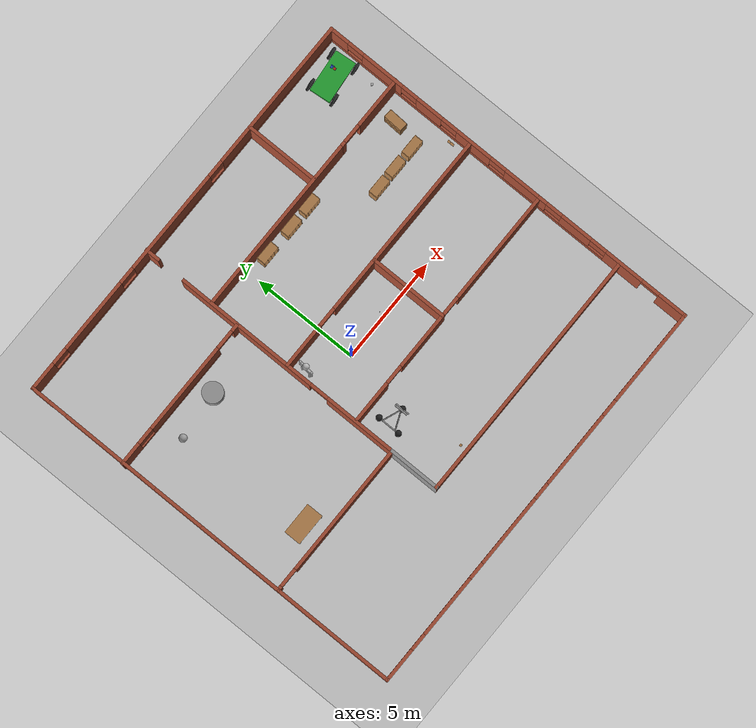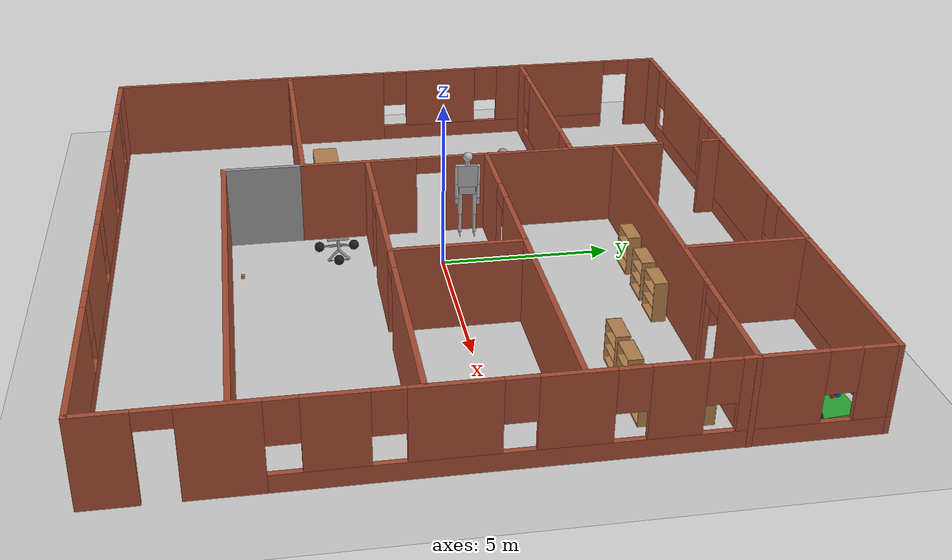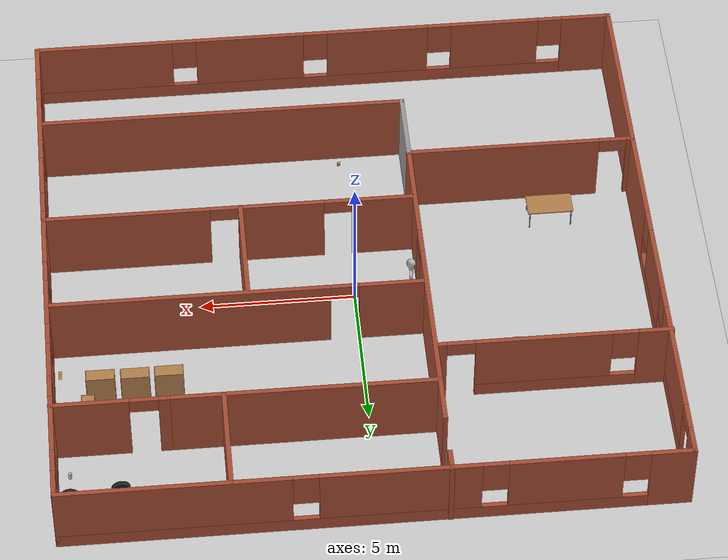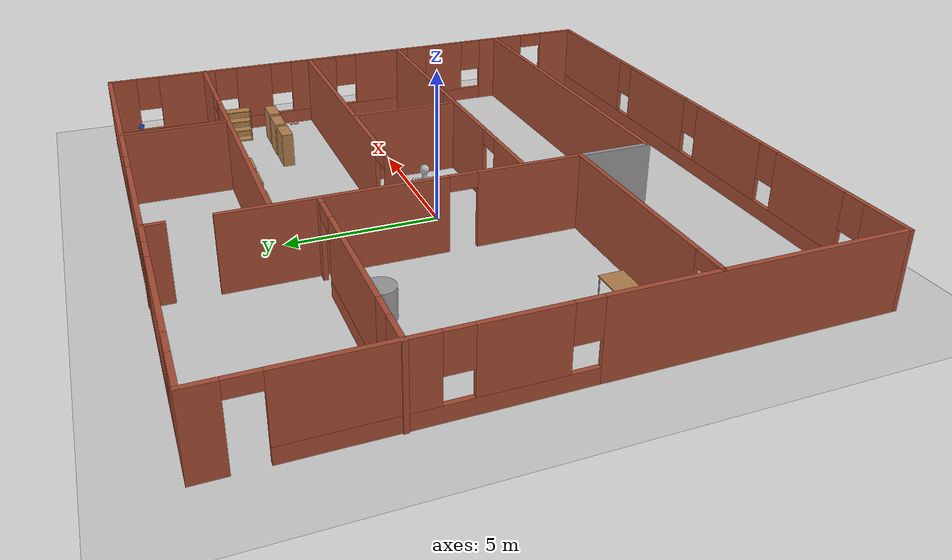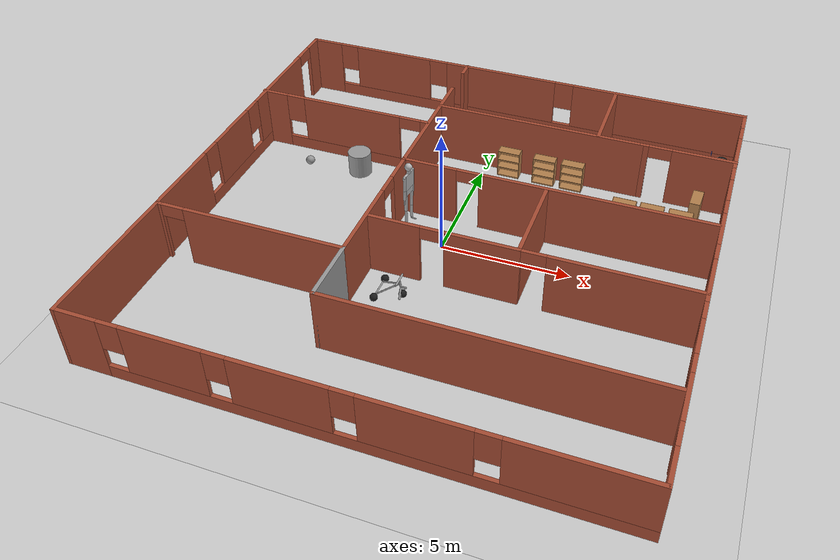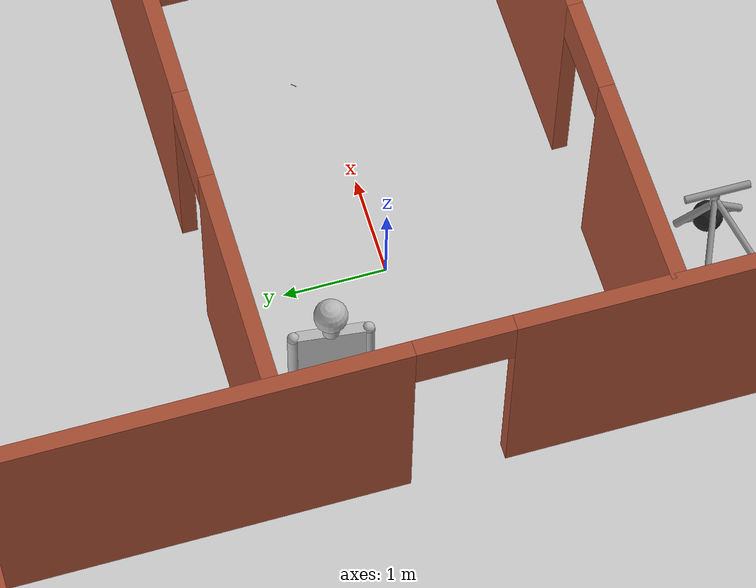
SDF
<sdf version="1.7">
 <world name="default">
  <light name="sun" type="directional">
   <pose>0 0 10 0 -0 0</pose>
   <diffuse>0.8 0.8 0.8 1</diffuse>
   <specular>0.2 0.2 0.2 1</specular>
   <attenuation>
    <range>1000</range>
    <constant>0.9</constant>
    <linear>0.01</linear>
    <quadratic>0.001</quadratic>
   </attenuation>
   <direction>-0.5 0.1 -0.9</direction>
   <spot><inner_angle>0</inner_angle><outer_angle>0</outer_angle><falloff>0</falloff></spot>
  </light>
  <model name="ground_plane">
   <static>1</static>
   <link name="link">
    <collision name="collision">
     <geometry><plane><normal>0 0 1</normal><size>100 100</size></plane></geometry>
     <surface>
      <contact><collide_bitmask>65535</collide_bitmask></contact>
      <friction><ode><mu>100</mu><mu2>50</mu2></ode></friction>
     </surface>
    </collision>
    <visual name="visual">
     <cast_shadows>0</cast_shadows>
     <geometry><plane><normal>0 0 1</normal><size>100 100</size></plane></geometry>
     <material>
      <script><uri>file://media/materials/scripts/gazebo.material</uri><name>Gazebo/Grey</name></script>
     </material>
    </visual>
   </link>
  </model>
  <gravity>0 0 -9.8</gravity>
  <magnetic_field>6e-06 2.3e-05 -4.2e-05</magnetic_field>
  <atmosphere type="adiabatic"/>
  <physics type="ode">
   <max_step_size>0.001</max_step_size>
   <real_time_factor>1</real_time_factor>
   <real_time_update_rate>1000</real_time_update_rate>
  </physics>
  <scene><ambient>0.4 0.4 0.4 1</ambient><background>0.7 0.7 0.7 1</background><shadows>1</shadows></scene>
  <audio><device>default</device></audio>
  <spherical_coordinates>
   <surface_model>EARTH_WGS84</surface_model>
   <latitude_deg>0</latitude_deg>
   <longitude_deg>0</longitude_deg>
   <elevation>0</elevation>
   <heading_deg>0</heading_deg>
  </spherical_coordinates>
  <model name="Robo_house">
   <pose>0.166 -0.2695 0 0 -0 0</pose>
   <link name="Wall_15">
    <pose>0.017 -9.4375 0 0 -0 0</pose>
    <visual name="Wall_15_Visual_0">
     <pose>-8.91507 0 1.25 0 -0 0</pose>
     <geometry><box><size>1.66987 0.15 2.5</size></box></geometry>
     <material>
      <script><uri>file://media/materials/scripts/gazebo.material</uri><name>Gazebo/Bricks</name></script>
      <ambient>1 1 1 1</ambient>
     </material>
     <meta><layer>0</layer></meta>
    </visual>
    <collision name="Wall_15_Collision_0">
     <geometry><box><size>1.66987 0.15 2.5</size></box></geometry>
     <pose>-8.91507 0 1.25 0 -0 0</pose>
    </collision>
    <visual name="Wall_15_Visual_1">
     <pose>0.834934 0 0.25 0 -0 0</pose>
     <geometry><box><size>17.8301 0.15 0.5</size></box></geometry>
     <material>
      <script><uri>file://media/materials/scripts/gazebo.material</uri><name>Gazebo/Bricks</name></script>
      <ambient>1 1 1 1</ambient>
     </material>
     <meta><layer>0</layer></meta>
    </visual>
    <collision name="Wall_15_Collision_1">
     <geometry><box><size>17.8301 0.15 0.5</size></box></geometry>
     <pose>0.834934 0 0.25 0 -0 0</pose>
    </collision>
    <visual name="Wall_15_Visual_2">
     <pose>-5.79807 0 1.5 0 -0 0</pose>
     <geometry><box><size>2.96413 0.15 2</size></box></geometry>
     <material>
      <script><uri>file://media/materials/scripts/gazebo.material</uri><name>Gazebo/Bricks</name></script>
      <ambient>1 1 1 1</ambient>
     </material>
     <meta><layer>0</layer></meta>
    </visual>
    <collision name="Wall_15_Collision_2">
     <geometry><box><size>2.96413 0.15 2</size></box></geometry>
     <pose>-5.79807 0 1.5 0 -0 0</pose>
    </collision>
    <visual name="Wall_15_Visual_3">
     <pose>-1.80528 0 1.5 0 -0 0</pose>
     <geometry><box><size>3.42145 0.15 2</size></box></geometry>
     <material>
      <script><uri>file://media/materials/scripts/gazebo.material</uri><name>Gazebo/Bricks</name></script>
      <ambient>1 1 1 1</ambient>
     </material>
     <meta><layer>0</layer></meta>
    </visual>
    <collision name="Wall_15_Collision_3">
     <geometry><box><size>3.42145 0.15 2</size></box></geometry>
     <pose>-1.80528 0 1.5 0 -0 0</pose>
    </collision>
    <visual name="Wall_15_Visual_4">
     <pose>2.52171 0 1.5 0 -0 0</pose>
     <geometry><box><size>3.63252 0.15 2</size></box></geometry>
     <material>
      <script><uri>file://media/materials/scripts/gazebo.material</uri><name>Gazebo/Bricks</name></script>
      <ambient>1 1 1 1</ambient>
     </material>
     <meta><layer>0</layer></meta>
    </visual>
    <collision name="Wall_15_Collision_4">
     <geometry><box><size>3.63252 0.15 2</size></box></geometry>
     <pose>2.52171 0 1.5 0 -0 0</pose>
    </collision>
    <visual name="Wall_15_Visual_5">
     <pose>7.44398 0 1.5 0 -0 0</pose>
     <geometry><box><size>4.61203 0.15 2</size></box></geometry>
     <material>
      <script><uri>file://media/materials/scripts/gazebo.material</uri><name>Gazebo/Bricks</name></script>
      <ambient>1 1 1 1</ambient>
     </material>
     <meta><layer>0</layer></meta>
    </visual>
    <collision name="Wall_15_Collision_5">
     <geometry><box><size>4.61203 0.15 2</size></box></geometry>
     <pose>7.44398 0 1.5 0 -0 0</pose>
    </collision>
    <visual name="Wall_15_Visual_6">
     <pose>-7.68013 0 1.9 0 -0 0</pose>
     <geometry><box><size>0.8 0.15 1.2</size></box></geometry>
     <material>
      <script><uri>file://media/materials/scripts/gazebo.material</uri><name>Gazebo/Bricks</name></script>
      <ambient>1 1 1 1</ambient>
     </material>
     <meta><layer>0</layer></meta>
    </visual>
    <collision name="Wall_15_Collision_6">
     <geometry><box><size>0.8 0.15 1.2</size></box></geometry>
     <pose>-7.68013 0 1.9 0 -0 0</pose>
    </collision>
    <visual name="Wall_15_Visual_7">
     <pose>-3.91601 0 1.9 0 -0 0</pose>
     <geometry><box><size>0.8 0.15 1.2</size></box></geometry>
     <material>
      <script><uri>file://media/materials/scripts/gazebo.material</uri><name>Gazebo/Bricks</name></script>
      <ambient>1 1 1 1</ambient>
     </material>
     <meta><layer>0</layer></meta>
    </visual>
    <collision name="Wall_15_Collision_7">
     <geometry><box><size>0.8 0.15 1.2</size></box></geometry>
     <pose>-3.91601 0 1.9 0 -0 0</pose>
    </collision>
    <visual name="Wall_15_Visual_8">
     <pose>0.305447 0 1.9 0 -0 0</pose>
     <geometry><box><size>0.8 0.15 1.2</size></box></geometry>
     <material>
      <script><uri>file://media/materials/scripts/gazebo.material</uri><name>Gazebo/Bricks</name></script>
      <ambient>1 1 1 1</ambient>
     </material>
     <meta><layer>0</layer></meta>
    </visual>
    <collision name="Wall_15_Collision_8">
     <geometry><box><size>0.8 0.15 1.2</size></box></geometry>
     <pose>0.305447 0 1.9 0 -0 0</pose>
    </collision>
    <visual name="Wall_15_Visual_9">
     <pose>4.73797 0 1.9 0 -0 0</pose>
     <geometry><box><size>0.8 0.15 1.2</size></box></geometry>
     <material>
      <script><uri>file://media/materials/scripts/gazebo.material</uri><name>Gazebo/Bricks</name></script>
      <ambient>1 1 1 1</ambient>
     </material>
     <meta><layer>0</layer></meta>
    </visual>
    <collision name="Wall_15_Collision_9">
     <geometry><box><size>0.8 0.15 1.2</size></box></geometry>
     <pose>4.73797 0 1.9 0 -0 0</pose>
    </collision>
   </link>
   <link name="Wall_16">
    <pose>9.692 -0.0125 0 0 -0 1.5708</pose>
    <visual name="Wall_16_Visual_0">
     <pose>-8.77922 0 1.25 0 -0 0</pose>
     <geometry><box><size>1.44155 0.15 2.5</size></box></geometry>
     <material>
      <script><uri>file://media/materials/scripts/gazebo.material</uri><name>Gazebo/Bricks</name></script>
      <ambient>1 1 1 1</ambient>
     </material>
     <meta><layer>0</layer></meta>
    </visual>
    <collision name="Wall_16_Collision_0">
     <geometry><box><size>1.44155 0.15 2.5</size></box></geometry>
     <pose>-8.77922 0 1.25 0 -0 0</pose>
    </collision>
    <visual name="Wall_16_Visual_1">
     <pose>-6.20712 0 1.25 0 -0 0</pose>
     <geometry><box><size>1.90264 0.15 2.5</size></box></geometry>
     <material>
      <script><uri>file://media/materials/scripts/gazebo.material</uri><name>Gazebo/Bricks</name></script>
      <ambient>1 1 1 1</ambient>
     </material>
     <meta><layer>0</layer></meta>
    </visual>
    <collision name="Wall_16_Collision_1">
     <geometry><box><size>1.90264 0.15 2.5</size></box></geometry>
     <pose>-6.20712 0 1.25 0 -0 0</pose>
    </collision>
    <visual name="Wall_16_Visual_2">
     <pose>2.1221 0 0.25 0 -0 0</pose>
     <geometry><box><size>14.7558 0.15 0.5</size></box></geometry>
     <material>
      <script><uri>file://media/materials/scripts/gazebo.material</uri><name>Gazebo/Bricks</name></script>
      <ambient>1 1 1 1</ambient>
     </material>
     <meta><layer>0</layer></meta>
    </visual>
    <collision name="Wall_16_Collision_2">
     <geometry><box><size>14.7558 0.15 0.5</size></box></geometry>
     <pose>2.1221 0 0.25 0 -0 0</pose>
    </collision>
    <visual name="Wall_16_Visual_3">
     <pose>-3.67427 0 1.5 0 -0 0</pose>
     <geometry><box><size>1.56306 0.15 2</size></box></geometry>
     <material>
      <script><uri>file://media/materials/scripts/gazebo.material</uri><name>Gazebo/Bricks</name></script>
      <ambient>1 1 1 1</ambient>
     </material>
     <meta><layer>0</layer></meta>
    </visual>
    <collision name="Wall_16_Collision_3">
     <geometry><box><size>1.56306 0.15 2</size></box></geometry>
     <pose>-3.67427 0 1.5 0 -0 0</pose>
    </collision>
    <visual name="Wall_16_Visual_4">
     <pose>-1.00069 0 1.5 0 -0 0</pose>
     <geometry><box><size>2.18411 0.15 2</size></box></geometry>
     <material>
      <script><uri>file://media/materials/scripts/gazebo.material</uri><name>Gazebo/Bricks</name></script>
      <ambient>1 1 1 1</ambient>
     </material>
     <meta><layer>0</layer></meta>
    </visual>
    <collision name="Wall_16_Collision_4">
     <geometry><box><size>2.18411 0.15 2</size></box></geometry>
     <pose>-1.00069 0 1.5 0 -0 0</pose>
    </collision>
    <visual name="Wall_16_Visual_5">
     <pose>1.79027 0 1.5 0 -0 0</pose>
     <geometry><box><size>1.79781 0.15 2</size></box></geometry>
     <material>
      <script><uri>file://media/materials/scripts/gazebo.material</uri><name>Gazebo/Bricks</name></script>
      <ambient>1 1 1 1</ambient>
     </material>
     <meta><layer>0</layer></meta>
    </visual>
    <collision name="Wall_16_Collision_5">
     <geometry><box><size>1.79781 0.15 2</size></box></geometry>
     <pose>1.79027 0 1.5 0 -0 0</pose>
    </collision>
    <visual name="Wall_16_Visual_6">
     <pose>4.15524 0 1.5 0 -0 0</pose>
     <geometry><box><size>1.33214 0.15 2</size></box></geometry>
     <material>
      <script><uri>file://media/materials/scripts/gazebo.material</uri><name>Gazebo/Bricks</name></script>
      <ambient>1 1 1 1</ambient>
     </material>
     <meta><layer>0</layer></meta>
    </visual>
    <collision name="Wall_16_Collision_6">
     <geometry><box><size>1.33214 0.15 2</size></box></geometry>
     <pose>4.15524 0 1.5 0 -0 0</pose>
    </collision>
    <visual name="Wall_16_Visual_7">
     <pose>6.66355 0 1.5 0 -0 0</pose>
     <geometry><box><size>2.08446 0.15 2</size></box></geometry>
     <material>
      <script><uri>file://media/materials/scripts/gazebo.material</uri><name>Gazebo/Bricks</name></script>
      <ambient>1 1 1 1</ambient>
     </material>
     <meta><layer>0</layer></meta>
    </visual>
    <collision name="Wall_16_Collision_7">
     <geometry><box><size>2.08446 0.15 2</size></box></geometry>
     <pose>6.66355 0 1.5 0 -0 0</pose>
    </collision>
    <visual name="Wall_16_Visual_8">
     <pose>9.00289 0 1.5 0 -0 0</pose>
     <geometry><box><size>0.99422 0.15 2</size></box></geometry>
     <material>
      <script><uri>file://media/materials/scripts/gazebo.material</uri><name>Gazebo/Bricks</name></script>
      <ambient>1 1 1 1</ambient>
     </material>
     <meta><layer>0</layer></meta>
    </visual>
    <collision name="Wall_16_Collision_8">
     <geometry><box><size>0.99422 0.15 2</size></box></geometry>
     <pose>9.00289 0 1.5 0 -0 0</pose>
    </collision>
    <visual name="Wall_16_Visual_9">
     <pose>-4.8558 0 1.9 0 -0 0</pose>
     <geometry><box><size>0.8 0.15 1.2</size></box></geometry>
     <material>
      <script><uri>file://media/materials/scripts/gazebo.material</uri><name>Gazebo/Bricks</name></script>
      <ambient>1 1 1 1</ambient>
     </material>
     <meta><layer>0</layer></meta>
    </visual>
    <collision name="Wall_16_Collision_9">
     <geometry><box><size>0.8 0.15 1.2</size></box></geometry>
     <pose>-4.8558 0 1.9 0 -0 0</pose>
    </collision>
    <visual name="Wall_16_Visual_10">
     <pose>-2.49274 0 1.9 0 -0 0</pose>
     <geometry><box><size>0.8 0.15 1.2</size></box></geometry>
     <material>
      <script><uri>file://media/materials/scripts/gazebo.material</uri><name>Gazebo/Bricks</name></script>
      <ambient>1 1 1 1</ambient>
     </material>
     <meta><layer>0</layer></meta>
    </visual>
    <collision name="Wall_16_Collision_10">
     <geometry><box><size>0.8 0.15 1.2</size></box></geometry>
     <pose>-2.49274 0 1.9 0 -0 0</pose>
    </collision>
    <visual name="Wall_16_Visual_11">
     <pose>0.491371 0 1.9 0 -0 0</pose>
     <geometry><box><size>0.8 0.15 1.2</size></box></geometry>
     <material>
      <script><uri>file://media/materials/scripts/gazebo.material</uri><name>Gazebo/Bricks</name></script>
      <ambient>1 1 1 1</ambient>
     </material>
     <meta><layer>0</layer></meta>
    </visual>
    <collision name="Wall_16_Collision_11">
     <geometry><box><size>0.8 0.15 1.2</size></box></geometry>
     <pose>0.491371 0 1.9 0 -0 0</pose>
    </collision>
    <visual name="Wall_16_Visual_12">
     <pose>3.08918 0 1.9 0 -0 0</pose>
     <geometry><box><size>0.8 0.15 1.2</size></box></geometry>
     <material>
      <script><uri>file://media/materials/scripts/gazebo.material</uri><name>Gazebo/Bricks</name></script>
      <ambient>1 1 1 1</ambient>
     </material>
     <meta><layer>0</layer></meta>
    </visual>
    <collision name="Wall_16_Collision_12">
     <geometry><box><size>0.8 0.15 1.2</size></box></geometry>
     <pose>3.08918 0 1.9 0 -0 0</pose>
    </collision>
    <visual name="Wall_16_Visual_13">
     <pose>5.22131 0 1.9 0 -0 0</pose>
     <geometry><box><size>0.8 0.15 1.2</size></box></geometry>
     <material>
      <script><uri>file://media/materials/scripts/gazebo.material</uri><name>Gazebo/Bricks</name></script>
      <ambient>1 1 1 1</ambient>
     </material>
     <meta><layer>0</layer></meta>
    </visual>
    <collision name="Wall_16_Collision_13">
     <geometry><box><size>0.8 0.15 1.2</size></box></geometry>
     <pose>5.22131 0 1.9 0 -0 0</pose>
    </collision>
    <visual name="Wall_16_Visual_14">
     <pose>8.10578 0 1.9 0 -0 0</pose>
     <geometry><box><size>0.8 0.15 1.2</size></box></geometry>
     <material>
      <script><uri>file://media/materials/scripts/gazebo.material</uri><name>Gazebo/Bricks</name></script>
      <ambient>1 1 1 1</ambient>
     </material>
     <meta><layer>0</layer></meta>
    </visual>
    <collision name="Wall_16_Collision_14">
     <geometry><box><size>0.8 0.15 1.2</size></box></geometry>
     <pose>8.10578 0 1.9 0 -0 0</pose>
    </collision>
    <visual name="Wall_16_Visual_15">
     <pose>-7.60845 0 2.25 0 -0 0</pose>
     <geometry><box><size>0.9 0.15 0.5</size></box></geometry>
     <material>
      <script><uri>file://media/materials/scripts/gazebo.material</uri><name>Gazebo/Bricks</name></script>
      <ambient>1 1 1 1</ambient>
     </material>
     <meta><layer>0</layer></meta>
    </visual>
    <collision name="Wall_16_Collision_15">
     <geometry><box><size>0.9 0.15 0.5</size></box></geometry>
     <pose>-7.60845 0 2.25 0 -0 0</pose>
    </collision>
   </link>
   <link name="Wall_20">
    <pose>-9.658 -0.0125 0 0 -0 1.5708</pose>
    <visual name="Wall_20_Visual_0">
     <pose>-4.92846 0 1.25 0 -0 0</pose>
     <geometry><box><size>9.14308 0.15 2.5</size></box></geometry>
     <material>
      <script><uri>file://media/materials/scripts/gazebo.material</uri><name>Gazebo/Bricks</name></script>
      <ambient>1 1 1 1</ambient>
     </material>
     <meta><layer>0</layer></meta>
    </visual>
    <collision name="Wall_20_Collision_0">
     <geometry><box><size>9.14308 0.15 2.5</size></box></geometry>
     <pose>-4.92846 0 1.25 0 -0 0</pose>
    </collision>
    <visual name="Wall_20_Visual_1">
     <pose>9.02608 0 1.25 0 -0 0</pose>
     <geometry><box><size>0.947833 0.15 2.5</size></box></geometry>
     <material>
      <script><uri>file://media/materials/scripts/gazebo.material</uri><name>Gazebo/Bricks</name></script>
      <ambient>1 1 1 1</ambient>
     </material>
     <meta><layer>0</layer></meta>
    </visual>
    <collision name="Wall_20_Collision_1">
     <geometry><box><size>0.947833 0.15 2.5</size></box></geometry>
     <pose>9.02608 0 1.25 0 -0 0</pose>
    </collision>
    <visual name="Wall_20_Visual_2">
     <pose>3.64762 0 0.25 0 -0 0</pose>
     <geometry><box><size>8.00909 0.15 0.5</size></box></geometry>
     <material>
      <script><uri>file://media/materials/scripts/gazebo.material</uri><name>Gazebo/Bricks</name></script>
      <ambient>1 1 1 1</ambient>
     </material>
     <meta><layer>0</layer></meta>
    </visual>
    <collision name="Wall_20_Collision_2">
     <geometry><box><size>8.00909 0.15 0.5</size></box></geometry>
     <pose>3.64762 0 0.25 0 -0 0</pose>
    </collision>
    <visual name="Wall_20_Visual_3">
     <pose>1.67438 0 1.5 0 -0 0</pose>
     <geometry><box><size>2.46259 0.15 2</size></box></geometry>
     <material>
      <script><uri>file://media/materials/scripts/gazebo.material</uri><name>Gazebo/Bricks</name></script>
      <ambient>1 1 1 1</ambient>
     </material>
     <meta><layer>0</layer></meta>
    </visual>
    <collision name="Wall_20_Collision_3">
     <geometry><box><size>2.46259 0.15 2</size></box></geometry>
     <pose>1.67438 0 1.5 0 -0 0</pose>
    </collision>
    <visual name="Wall_20_Visual_4">
     <pose>5.67892 0 1.5 0 -0 0</pose>
     <geometry><box><size>3.9465 0.15 2</size></box></geometry>
     <material>
      <script><uri>file://media/materials/scripts/gazebo.material</uri><name>Gazebo/Bricks</name></script>
      <ambient>1 1 1 1</ambient>
     </material>
     <meta><layer>0</layer></meta>
    </visual>
    <collision name="Wall_20_Collision_4">
     <geometry><box><size>3.9465 0.15 2</size></box></geometry>
     <pose>5.67892 0 1.5 0 -0 0</pose>
    </collision>
    <visual name="Wall_20_Visual_5">
     <pose>0.04308 0 1.9 0 -0 0</pose>
     <geometry><box><size>0.8 0.15 1.2</size></box></geometry>
     <material>
      <script><uri>file://media/materials/scripts/gazebo.material</uri><name>Gazebo/Bricks</name></script>
      <ambient>1 1 1 1</ambient>
     </material>
     <meta><layer>0</layer></meta>
    </visual>
    <collision name="Wall_20_Collision_5">
     <geometry><box><size>0.8 0.15 1.2</size></box></geometry>
     <pose>0.04308 0 1.9 0 -0 0</pose>
    </collision>
    <visual name="Wall_20_Visual_6">
     <pose>3.30567 0 1.9 0 -0 0</pose>
     <geometry><box><size>0.8 0.15 1.2</size></box></geometry>
     <material>
      <script><uri>file://media/materials/scripts/gazebo.material</uri><name>Gazebo/Bricks</name></script>
      <ambient>1 1 1 1</ambient>
     </material>
     <meta><layer>0</layer></meta>
    </visual>
    <collision name="Wall_20_Collision_6">
     <geometry><box><size>0.8 0.15 1.2</size></box></geometry>
     <pose>3.30567 0 1.9 0 -0 0</pose>
    </collision>
    <visual name="Wall_20_Visual_7">
     <pose>8.10217 0 2.25 0 -0 0</pose>
     <geometry><box><size>0.9 0.15 0.5</size></box></geometry>
     <material>
      <script><uri>file://media/materials/scripts/gazebo.material</uri><name>Gazebo/Bricks</name></script>
      <ambient>1 1 1 1</ambient>
     </material>
     <meta><layer>0</layer></meta>
    </visual>
    <collision name="Wall_20_Collision_7">
     <geometry><box><size>0.9 0.15 0.5</size></box></geometry>
     <pose>8.10217 0 2.25 0 -0 0</pose>
    </collision>
   </link>
   <link name="Wall_21">
    <pose>0.017 9.4125 0 0 -0 0</pose>
    <visual name="Wall_21_Visual_0">
     <pose>-9.05411 0 1.25 0 -0 0</pose>
     <geometry><box><size>1.39177 0.15 2.5</size></box></geometry>
     <material>
      <script><uri>file://media/materials/scripts/gazebo.material</uri><name>Gazebo/Bricks</name></script>
      <ambient>1 1 1 1</ambient>
     </material>
     <meta><layer>0</layer></meta>
    </visual>
    <collision name="Wall_21_Collision_0">
     <geometry><box><size>1.39177 0.15 2.5</size></box></geometry>
     <pose>-9.05411 0 1.25 0 -0 0</pose>
    </collision>
    <visual name="Wall_21_Visual_1">
     <pose>0.695886 0 0.25 0 -0 0</pose>
     <geometry><box><size>18.1082 0.15 0.5</size></box></geometry>
     <material>
      <script><uri>file://media/materials/scripts/gazebo.material</uri><name>Gazebo/Bricks</name></script>
      <ambient>1 1 1 1</ambient>
     </material>
     <meta><layer>0</layer></meta>
    </visual>
    <collision name="Wall_21_Collision_1">
     <geometry><box><size>18.1082 0.15 0.5</size></box></geometry>
     <pose>0.695886 0 0.25 0 -0 0</pose>
    </collision>
    <visual name="Wall_21_Visual_2">
     <pose>-5.79711 0 1.5 0 -0 0</pose>
     <geometry><box><size>3.52224 0.15 2</size></box></geometry>
     <material>
      <script><uri>file://media/materials/scripts/gazebo.material</uri><name>Gazebo/Bricks</name></script>
      <ambient>1 1 1 1</ambient>
     </material>
     <meta><layer>0</layer></meta>
    </visual>
    <collision name="Wall_21_Collision_2">
     <geometry><box><size>3.52224 0.15 2</size></box></geometry>
     <pose>-5.79711 0 1.5 0 -0 0</pose>
    </collision>
    <visual name="Wall_21_Visual_3">
     <pose>-0.763639 0 1.5 0 -0 0</pose>
     <geometry><box><size>4.94469 0.15 2</size></box></geometry>
     <material>
      <script><uri>file://media/materials/scripts/gazebo.material</uri><name>Gazebo/Bricks</name></script>
      <ambient>1 1 1 1</ambient>
     </material>
     <meta><layer>0</layer></meta>
    </visual>
    <collision name="Wall_21_Collision_3">
     <geometry><box><size>4.94469 0.15 2</size></box></geometry>
     <pose>-0.763639 0 1.5 0 -0 0</pose>
    </collision>
    <visual name="Wall_21_Visual_4">
     <pose>6.12935 0 1.5 0 -0 0</pose>
     <geometry><box><size>7.24129 0.15 2</size></box></geometry>
     <material>
      <script><uri>file://media/materials/scripts/gazebo.material</uri><name>Gazebo/Bricks</name></script>
      <ambient>1 1 1 1</ambient>
     </material>
     <meta><layer>0</layer></meta>
    </visual>
    <collision name="Wall_21_Collision_4">
     <geometry><box><size>7.24129 0.15 2</size></box></geometry>
     <pose>6.12935 0 1.5 0 -0 0</pose>
    </collision>
    <visual name="Wall_21_Visual_5">
     <pose>-7.95823 0 1.9 0 -0 0</pose>
     <geometry><box><size>0.8 0.15 1.2</size></box></geometry>
     <material>
      <script><uri>file://media/materials/scripts/gazebo.material</uri><name>Gazebo/Bricks</name></script>
      <ambient>1 1 1 1</ambient>
     </material>
     <meta><layer>0</layer></meta>
    </visual>
    <collision name="Wall_21_Collision_5">
     <geometry><box><size>0.8 0.15 1.2</size></box></geometry>
     <pose>-7.95823 0 1.9 0 -0 0</pose>
    </collision>
    <visual name="Wall_21_Visual_6">
     <pose>-3.63598 0 1.9 0 -0 0</pose>
     <geometry><box><size>0.8 0.15 1.2</size></box></geometry>
     <material>
      <script><uri>file://media/materials/scripts/gazebo.material</uri><name>Gazebo/Bricks</name></script>
      <ambient>1 1 1 1</ambient>
     </material>
     <meta><layer>0</layer></meta>
    </visual>
    <collision name="Wall_21_Collision_6">
     <geometry><box><size>0.8 0.15 1.2</size></box></geometry>
     <pose>-3.63598 0 1.9 0 -0 0</pose>
    </collision>
    <visual name="Wall_21_Visual_7">
     <pose>2.10871 0 1.9 0 -0 0</pose>
     <geometry><box><size>0.8 0.15 1.2</size></box></geometry>
     <material>
      <script><uri>file://media/materials/scripts/gazebo.material</uri><name>Gazebo/Bricks</name></script>
      <ambient>1 1 1 1</ambient>
     </material>
     <meta><layer>0</layer></meta>
    </visual>
    <collision name="Wall_21_Collision_7">
     <geometry><box><size>0.8 0.15 1.2</size></box></geometry>
     <pose>2.10871 0 1.9 0 -0 0</pose>
    </collision>
   </link>
   <link name="Wall_23">
    <pose>-5.961 -3.6535 0 0 -0 0</pose>
    <visual name="Wall_23_Visual_0">
     <pose>-3.62205 0 1.25 0 -0 0</pose>
     <geometry><box><size>0.255896 0.15 2.5</size></box></geometry>
     <material>
      <script><uri>file://media/materials/scripts/gazebo.material</uri><name>Gazebo/Bricks</name></script>
      <ambient>1 1 1 1</ambient>
     </material>
     <meta><layer>0</layer></meta>
    </visual>
    <collision name="Wall_23_Collision_0">
     <geometry><box><size>0.255896 0.15 2.5</size></box></geometry>
     <pose>-3.62205 0 1.25 0 -0 0</pose>
    </collision>
    <visual name="Wall_23_Visual_1">
     <pose>0.577948 0 1.25 0 -0 0</pose>
     <geometry><box><size>6.3441 0.15 2.5</size></box></geometry>
     <material>
      <script><uri>file://media/materials/scripts/gazebo.material</uri><name>Gazebo/Bricks</name></script>
      <ambient>1 1 1 1</ambient>
     </material>
     <meta><layer>0</layer></meta>
    </visual>
    <collision name="Wall_23_Collision_1">
     <geometry><box><size>6.3441 0.15 2.5</size></box></geometry>
     <pose>0.577948 0 1.25 0 -0 0</pose>
    </collision>
    <visual name="Wall_23_Visual_2">
     <pose>-3.0441 0 2.25 0 -0 0</pose>
     <geometry><box><size>0.9 0.15 0.5</size></box></geometry>
     <material>
      <script><uri>file://media/materials/scripts/gazebo.material</uri><name>Gazebo/Bricks</name></script>
      <ambient>1 1 1 1</ambient>
     </material>
     <meta><layer>0</layer></meta>
    </visual>
    <collision name="Wall_23_Collision_2">
     <geometry><box><size>0.9 0.15 0.5</size></box></geometry>
     <pose>-3.0441 0 2.25 0 -0 0</pose>
    </collision>
   </link>
   <link name="Wall_24">
    <collision name="Wall_24_Collision">
     <geometry><box><size>2.5 0.15 2.5</size></box></geometry>
     <pose>0 0 1.25 0 -0 0</pose>
    </collision>
    <visual name="Wall_24_Visual">
     <pose>0 0 1.25 0 -0 0</pose>
     <geometry><box><size>2.5 0.15 2.5</size></box></geometry>
     <material>
      <script><uri>file://media/materials/scripts/gazebo.material</uri><name>Gazebo/Grey</name></script>
      <ambient>1 1 1 1</ambient>
     </material>
     <meta><layer>0</layer></meta>
    </visual>
    <pose>-2.286 -4.8285 0 0 -0 -1.5708</pose>
   </link>
   <link name="Wall_25">
    <collision name="Wall_25_Collision">
     <geometry><box><size>12 0.15 2.5</size></box></geometry>
     <pose>0 0 1.25 0 -0 0</pose>
    </collision>
    <visual name="Wall_25_Visual">
     <pose>0 0 1.25 0 -0 0</pose>
     <geometry><box><size>12 0.15 2.5</size></box></geometry>
     <material>
      <script><uri>file://media/materials/scripts/gazebo.material</uri><name>Gazebo/Bricks</name></script>
      <ambient>1 1 1 1</ambient>
     </material>
     <meta><layer>0</layer></meta>
    </visual>
    <pose>3.639 -6.0035 0 0 -0 0</pose>
   </link>
   <link name="Wall_34">
    <pose>7.902 5.9825 0 0 -0 0</pose>
    <visual name="Wall_34_Visual_0">
     <pose>-1.6939 0 1.25 0 -0 0</pose>
     <geometry><box><size>0.362205 0.15 2.5</size></box></geometry>
     <material>
      <script><uri>file://media/materials/scripts/gazebo.material</uri><name>Gazebo/Bricks</name></script>
      <ambient>1 1 1 1</ambient>
     </material>
     <meta><layer>0</layer></meta>
    </visual>
    <collision name="Wall_34_Collision_0">
     <geometry><box><size>0.362205 0.15 2.5</size></box></geometry>
     <pose>-1.6939 0 1.25 0 -0 0</pose>
    </collision>
    <visual name="Wall_34_Visual_1">
     <pose>0.631102 0 1.25 0 -0 0</pose>
     <geometry><box><size>2.4878 0.15 2.5</size></box></geometry>
     <material>
      <script><uri>file://media/materials/scripts/gazebo.material</uri><name>Gazebo/Bricks</name></script>
      <ambient>1 1 1 1</ambient>
     </material>
     <meta><layer>0</layer></meta>
    </visual>
    <collision name="Wall_34_Collision_1">
     <geometry><box><size>2.4878 0.15 2.5</size></box></geometry>
     <pose>0.631102 0 1.25 0 -0 0</pose>
    </collision>
    <visual name="Wall_34_Visual_2">
     <pose>-1.06279 0 2.25 0 -0 0</pose>
     <geometry><box><size>0.9 0.15 0.5</size></box></geometry>
     <material>
      <script><uri>file://media/materials/scripts/gazebo.material</uri><name>Gazebo/Bricks</name></script>
      <ambient>1 1 1 1</ambient>
     </material>
     <meta><layer>0</layer></meta>
    </visual>
    <collision name="Wall_34_Collision_2">
     <geometry><box><size>0.9 0.15 0.5</size></box></geometry>
     <pose>-1.06279 0 2.25 0 -0 0</pose>
    </collision>
   </link>
   <link name="Wall_36">
    <pose>-2.286 1.8965 0 0 -0 1.5708</pose>
    <visual name="Wall_36_Visual_0">
     <pose>-3.87113 0 1.25 0 -0 0</pose>
     <geometry><box><size>3.50774 0.15 2.5</size></box></geometry>
     <material>
      <script><uri>file://media/materials/scripts/gazebo.material</uri><name>Gazebo/Bricks</name></script>
      <ambient>1 1 1 1</ambient>
     </material>
     <meta><layer>0</layer></meta>
    </visual>
    <collision name="Wall_36_Collision_0">
     <geometry><box><size>3.50774 0.15 2.5</size></box></geometry>
     <pose>-3.87113 0 1.25 0 -0 0</pose>
    </collision>
    <visual name="Wall_36_Visual_1">
     <pose>2.20387 0 1.25 0 -0 0</pose>
     <geometry><box><size>6.84226 0.15 2.5</size></box></geometry>
     <material>
      <script><uri>file://media/materials/scripts/gazebo.material</uri><name>Gazebo/Bricks</name></script>
      <ambient>1 1 1 1</ambient>
     </material>
     <meta><layer>0</layer></meta>
    </visual>
    <collision name="Wall_36_Collision_1">
     <geometry><box><size>6.84226 0.15 2.5</size></box></geometry>
     <pose>2.20387 0 1.25 0 -0 0</pose>
    </collision>
    <visual name="Wall_36_Visual_2">
     <pose>-1.66726 0 2.25 0 -0 0</pose>
     <geometry><box><size>0.9 0.15 0.5</size></box></geometry>
     <material>
      <script><uri>file://media/materials/scripts/gazebo.material</uri><name>Gazebo/Bricks</name></script>
      <ambient>1 1 1 1</ambient>
     </material>
     <meta><layer>0</layer></meta>
    </visual>
    <collision name="Wall_36_Collision_2">
     <geometry><box><size>0.9 0.15 0.5</size></box></geometry>
     <pose>-1.66726 0 2.25 0 -0 0</pose>
    </collision>
   </link>
   <link name="Wall_38">
    <collision name="Wall_38_Collision">
     <geometry><box><size>8.5 0.15 2.5</size></box></geometry>
     <pose>0 0 1.25 0 -0 0</pose>
    </collision>
    <visual name="Wall_38_Visual">
     <pose>0 0 1.25 0 -0 0</pose>
     <geometry><box><size>8.5 0.15 2.5</size></box></geometry>
     <material>
      <script><uri>file://media/materials/scripts/gazebo.material</uri><name>Gazebo/Bricks</name></script>
      <ambient>1 1 1 1</ambient>
     </material>
     <meta><layer>0</layer></meta>
    </visual>
    <pose>1.927 5.9825 0 0 -0 3.14159</pose>
   </link>
   <link name="Wall_44">
    <collision name="Wall_44_Collision">
     <geometry><box><size>0.75 0.15 2.5</size></box></geometry>
     <pose>0 0 1.25 0 -0 0</pose>
    </collision>
    <visual name="Wall_44_Visual">
     <pose>0 0 1.25 0 -0 0</pose>
     <geometry><box><size>0.75 0.15 2.5</size></box></geometry>
     <material>
      <script><uri>file://media/materials/scripts/gazebo.material</uri><name>Gazebo/Bricks</name></script>
      <ambient>1 1 1 1</ambient>
     </material>
     <meta><layer>0</layer></meta>
    </visual>
    <pose>-2.281 9.1375 0 0 -0 -1.5708</pose>
   </link>
   <link name="Wall_46">
    <pose>3.659 1.9305 0 0 -0 0</pose>
    <visual name="Wall_46_Visual_0">
     <pose>-4.90616 0 1.25 0 -0 0</pose>
     <geometry><box><size>2.18769 0.15 2.5</size></box></geometry>
     <material>
      <script><uri>file://media/materials/scripts/gazebo.material</uri><name>Gazebo/Bricks</name></script>
      <ambient>1 1 1 1</ambient>
     </material>
     <meta><layer>0</layer></meta>
    </visual>
    <collision name="Wall_46_Collision_0">
     <geometry><box><size>2.18769 0.15 2.5</size></box></geometry>
     <pose>-4.90616 0 1.25 0 -0 0</pose>
    </collision>
    <visual name="Wall_46_Visual_1">
     <pose>1.54384 0 1.25 0 -0 0</pose>
     <geometry><box><size>8.91231 0.15 2.5</size></box></geometry>
     <material>
      <script><uri>file://media/materials/scripts/gazebo.material</uri><name>Gazebo/Bricks</name></script>
      <ambient>1 1 1 1</ambient>
     </material>
     <meta><layer>0</layer></meta>
    </visual>
    <collision name="Wall_46_Collision_1">
     <geometry><box><size>8.91231 0.15 2.5</size></box></geometry>
     <pose>1.54384 0 1.25 0 -0 0</pose>
    </collision>
    <visual name="Wall_46_Visual_2">
     <pose>-3.36231 0 2.25 0 -0 0</pose>
     <geometry><box><size>0.9 0.15 0.5</size></box></geometry>
     <material>
      <script><uri>file://media/materials/scripts/gazebo.material</uri><name>Gazebo/Bricks</name></script>
      <ambient>1 1 1 1</ambient>
     </material>
     <meta><layer>0</layer></meta>
    </visual>
    <collision name="Wall_46_Collision_2">
     <geometry><box><size>0.9 0.15 0.5</size></box></geometry>
     <pose>-3.36231 0 2.25 0 -0 0</pose>
    </collision>
   </link>
   <link name="Wall_48">
    <pose>3.74 -1.7145 0 0 -0 0</pose>
    <visual name="Wall_48_Visual_0">
     <pose>-4.99272 0 1.25 0 -0 0</pose>
     <geometry><box><size>2.01456 0.15 2.5</size></box></geometry>
     <material>
      <script><uri>file://media/materials/scripts/gazebo.material</uri><name>Gazebo/Bricks</name></script>
      <ambient>1 1 1 1</ambient>
     </material>
     <meta><layer>0</layer></meta>
    </visual>
    <collision name="Wall_48_Collision_0">
     <geometry><box><size>2.01456 0.15 2.5</size></box></geometry>
     <pose>-4.99272 0 1.25 0 -0 0</pose>
    </collision>
    <visual name="Wall_48_Visual_1">
     <pose>-1.69471 0 1.25 0 -0 0</pose>
     <geometry><box><size>2.78146 0.15 2.5</size></box></geometry>
     <material>
      <script><uri>file://media/materials/scripts/gazebo.material</uri><name>Gazebo/Bricks</name></script>
      <ambient>1 1 1 1</ambient>
     </material>
     <meta><layer>0</layer></meta>
    </visual>
    <collision name="Wall_48_Collision_1">
     <geometry><box><size>2.78146 0.15 2.5</size></box></geometry>
     <pose>-1.69471 0 1.25 0 -0 0</pose>
    </collision>
    <visual name="Wall_48_Visual_2">
     <pose>3.29801 0 1.25 0 -0 0</pose>
     <geometry><box><size>5.40398 0.15 2.5</size></box></geometry>
     <material>
      <script><uri>file://media/materials/scripts/gazebo.material</uri><name>Gazebo/Bricks</name></script>
      <ambient>1 1 1 1</ambient>
     </material>
     <meta><layer>0</layer></meta>
    </visual>
    <collision name="Wall_48_Collision_2">
     <geometry><box><size>5.40398 0.15 2.5</size></box></geometry>
     <pose>3.29801 0 1.25 0 -0 0</pose>
    </collision>
    <visual name="Wall_48_Visual_3">
     <pose>-3.53544 0 2.25 0 -0 0</pose>
     <geometry><box><size>0.9 0.15 0.5</size></box></geometry>
     <material>
      <script><uri>file://media/materials/scripts/gazebo.material</uri><name>Gazebo/Bricks</name></script>
      <ambient>1 1 1 1</ambient>
     </material>
     <meta><layer>0</layer></meta>
    </visual>
    <collision name="Wall_48_Collision_3">
     <geometry><box><size>0.9 0.15 0.5</size></box></geometry>
     <pose>-3.53544 0 2.25 0 -0 0</pose>
    </collision>
    <visual name="Wall_48_Visual_4">
     <pose>0.146022 0 2.25 0 -0 0</pose>
     <geometry><box><size>0.9 0.15 0.5</size></box></geometry>
     <material>
      <script><uri>file://media/materials/scripts/gazebo.material</uri><name>Gazebo/Bricks</name></script>
      <ambient>1 1 1 1</ambient>
     </material>
     <meta><layer>0</layer></meta>
    </visual>
    <collision name="Wall_48_Collision_4">
     <geometry><box><size>0.9 0.15 0.5</size></box></geometry>
     <pose>0.146022 0 2.25 0 -0 0</pose>
    </collision>
   </link>
   <link name="Wall_56">
    <collision name="Wall_56_Collision">
     <geometry><box><size>3.75 0.15 2.5</size></box></geometry>
     <pose>0 0 1.25 0 -0 0</pose>
    </collision>
    <visual name="Wall_56_Visual">
     <pose>0 0 1.25 0 -0 0</pose>
     <geometry><box><size>3.75 0.15 2.5</size></box></geometry>
     <material>
      <script><uri>file://media/materials/scripts/gazebo.material</uri><name>Gazebo/Bricks</name></script>
      <ambient>1 1 1 1</ambient>
     </material>
     <meta><layer>0</layer></meta>
    </visual>
    <pose>3.36 0.0925 0 0 -0 -1.5708</pose>
   </link>
   <link name="Wall_58">
    <collision name="Wall_58_Collision">
     <geometry><box><size>3.5 0.15 2.5</size></box></geometry>
     <pose>0 0 1.25 0 -0 0</pose>
    </collision>
    <visual name="Wall_58_Visual">
     <pose>0 0 1.25 0 -0 0</pose>
     <geometry><box><size>3.5 0.15 2.5</size></box></geometry>
     <material>
      <script><uri>file://media/materials/scripts/gazebo.material</uri><name>Gazebo/Bricks</name></script>
      <ambient>1 1 1 1</ambient>
     </material>
     <meta><layer>0</layer></meta>
    </visual>
    <pose>4.374 7.6945 0 0 -0 -1.5708</pose>
   </link>
   <link name="Wall_60">
    <pose>-6.027 4.5905 0 0 -0 0</pose>
    <visual name="Wall_60_Visual_0">
     <pose>-3.18357 0 1.25 0 -0 0</pose>
     <geometry><box><size>1.13285 0.15 2.5</size></box></geometry>
     <material>
      <script><uri>file://media/materials/scripts/gazebo.material</uri><name>Gazebo/Bricks</name></script>
      <ambient>1 1 1 1</ambient>
     </material>
     <meta><layer>0</layer></meta>
    </visual>
    <collision name="Wall_60_Collision_0">
     <geometry><box><size>1.13285 0.15 2.5</size></box></geometry>
     <pose>-3.18357 0 1.25 0 -0 0</pose>
    </collision>
    <visual name="Wall_60_Visual_1">
     <pose>3.56381 0 1.25 0 -0 0</pose>
     <geometry><box><size>0.372382 0.15 2.5</size></box></geometry>
     <material>
      <script><uri>file://media/materials/scripts/gazebo.material</uri><name>Gazebo/Bricks</name></script>
      <ambient>1 1 1 1</ambient>
     </material>
     <meta><layer>0</layer></meta>
    </visual>
    <collision name="Wall_60_Collision_1">
     <geometry><box><size>0.372382 0.15 2.5</size></box></geometry>
     <pose>3.56381 0 1.25 0 -0 0</pose>
    </collision>
    <visual name="Wall_60_Visual_2">
     <pose>-0.069764 0 0.25 0 -0 0</pose>
     <geometry><box><size>5.09476 0.15 0.5</size></box></geometry>
     <material>
      <script><uri>file://media/materials/scripts/gazebo.material</uri><name>Gazebo/Bricks</name></script>
      <ambient>1 1 1 1</ambient>
     </material>
     <meta><layer>0</layer></meta>
    </visual>
    <collision name="Wall_60_Collision_2">
     <geometry><box><size>5.09476 0.15 0.5</size></box></geometry>
     <pose>-0.069764 0 0.25 0 -0 0</pose>
    </collision>
    <visual name="Wall_60_Visual_3">
     <pose>0.330236 0 1.5 0 -0 0</pose>
     <geometry><box><size>4.29476 0.15 2</size></box></geometry>
     <material>
      <script><uri>file://media/materials/scripts/gazebo.material</uri><name>Gazebo/Bricks</name></script>
      <ambient>1 1 1 1</ambient>
     </material>
     <meta><layer>0</layer></meta>
    </visual>
    <collision name="Wall_60_Collision_3">
     <geometry><box><size>4.29476 0.15 2</size></box></geometry>
     <pose>0.330236 0 1.5 0 -0 0</pose>
    </collision>
    <visual name="Wall_60_Visual_4">
     <pose>-2.21715 0 1.9 0 -0 0</pose>
     <geometry><box><size>0.8 0.15 1.2</size></box></geometry>
     <material>
      <script><uri>file://media/materials/scripts/gazebo.material</uri><name>Gazebo/Bricks</name></script>
      <ambient>1 1 1 1</ambient>
     </material>
     <meta><layer>0</layer></meta>
    </visual>
    <collision name="Wall_60_Collision_4">
     <geometry><box><size>0.8 0.15 1.2</size></box></geometry>
     <pose>-2.21715 0 1.9 0 -0 0</pose>
    </collision>
    <visual name="Wall_60_Visual_5">
     <pose>2.92762 0 2.25 0 -0 0</pose>
     <geometry><box><size>0.9 0.15 0.5</size></box></geometry>
     <material>
      <script><uri>file://media/materials/scripts/gazebo.material</uri><name>Gazebo/Bricks</name></script>
      <ambient>1 1 1 1</ambient>
     </material>
     <meta><layer>0</layer></meta>
    </visual>
    <collision name="Wall_60_Collision_5">
     <geometry><box><size>0.9 0.15 0.5</size></box></geometry>
     <pose>2.92762 0 2.25 0 -0 0</pose>
    </collision>
   </link>
   <static>1</static>
  </model>
  <model name="bookshelf">
   <static>1</static>
   <link name="link">
    <inertial><mass>1</mass></inertial>
    <collision name="back">
     <pose>0 0.005 0.6 0 -0 0</pose>
     <geometry><box><size>0.9 0.01 1.2</size></box></geometry>
    </collision>
    <visual name="visual1">
     <pose>0 0.005 0.6 0 -0 0</pose>
     <geometry><box><size>0.9 0.01 1.2</size></box></geometry>
     <material>
      <script><uri>file://media/materials/scripts/gazebo.material</uri><name>Gazebo/Wood</name></script>
     </material>
    </visual>
    <collision name="left_side">
     <pose>0.45 -0.195 0.6 0 -0 0</pose>
     <geometry><box><size>0.02 0.4 1.2</size></box></geometry>
    </collision>
    <visual name="visual2">
     <pose>0.45 -0.195 0.6 0 -0 0</pose>
     <geometry><box><size>0.02 0.4 1.2</size></box></geometry>
     <material>
      <script><uri>file://media/materials/scripts/gazebo.material</uri><name>Gazebo/Wood</name></script>
     </material>
    </visual>
    <collision name="right_side">
     <pose>-0.45 -0.195 0.6 0 -0 0</pose>
     <geometry><box><size>0.02 0.4 1.2</size></box></geometry>
    </collision>
    <visual name="visual3">
     <pose>-0.45 -0.195 0.6 0 -0 0</pose>
     <geometry><box><size>0.02 0.4 1.2</size></box></geometry>
     <material>
      <script><uri>file://media/materials/scripts/gazebo.material</uri><name>Gazebo/Wood</name></script>
     </material>
    </visual>
    <collision name="bottom">
     <pose>0 -0.195 0.03 0 -0 0</pose>
     <geometry><box><size>0.88 0.4 0.06</size></box></geometry>
    </collision>
    <visual name="visual4">
     <pose>0 -0.195 0.03 0 -0 0</pose>
     <geometry><box><size>0.88 0.4 0.06</size></box></geometry>
     <material>
      <script><uri>file://media/materials/scripts/gazebo.material</uri><name>Gazebo/Wood</name></script>
     </material>
    </visual>
    <collision name="top">
     <pose>0 -0.195 1.19 0 -0 0</pose>
     <geometry><box><size>0.88 0.4 0.02</size></box></geometry>
    </collision>
    <visual name="visual5">
     <pose>0 -0.195 1.19 0 -0 0</pose>
     <geometry><box><size>0.88 0.4 0.02</size></box></geometry>
     <material>
      <script><uri>file://media/materials/scripts/gazebo.material</uri><name>Gazebo/Wood</name></script>
     </material>
    </visual>
    <collision name="low_shelf">
     <pose>0 -0.195 0.43 0 -0 0</pose>
     <geometry><box><size>0.88 0.4 0.02</size></box></geometry>
    </collision>
    <visual name="visual6">
     <pose>0 -0.195 0.43 0 -0 0</pose>
     <geometry><box><size>0.88 0.4 0.02</size></box></geometry>
     <material>
      <script><uri>file://media/materials/scripts/gazebo.material</uri><name>Gazebo/Wood</name></script>
     </material>
    </visual>
    <collision name="high_shelf">
     <pose>0 -0.195 0.8 0 -0 0</pose>
     <geometry><box><size>0.88 0.4 0.02</size></box></geometry>
    </collision>
    <visual name="visual7">
     <pose>0 -0.195 0.8 0 -0 0</pose>
     <geometry><box><size>0.88 0.4 0.02</size></box></geometry>
     <material>
      <script><uri>file://media/materials/scripts/gazebo.material</uri><name>Gazebo/Wood</name></script>
     </material>
    </visual>
   </link>
   <pose>2.56224 5.52257 0 0 -0 0</pose>
  </model>
  <model name="bookshelf_0">
   <static>1</static>
   <link name="link">
    <inertial><mass>1</mass></inertial>
    <collision name="back">
     <pose>0 0.005 0.6 0 -0 0</pose>
     <geometry><box><size>0.9 0.01 1.2</size></box></geometry>
    </collision>
    <visual name="visual1">
     <pose>0 0.005 0.6 0 -0 0</pose>
     <geometry><box><size>0.9 0.01 1.2</size></box></geometry>
     <material>
      <script><uri>file://media/materials/scripts/gazebo.material</uri><name>Gazebo/Wood</name></script>
     </material>
    </visual>
    <collision name="left_side">
     <pose>0.45 -0.195 0.6 0 -0 0</pose>
     <geometry><box><size>0.02 0.4 1.2</size></box></geometry>
    </collision>
    <visual name="visual2">
     <pose>0.45 -0.195 0.6 0 -0 0</pose>
     <geometry><box><size>0.02 0.4 1.2</size></box></geometry>
     <material>
      <script><uri>file://media/materials/scripts/gazebo.material</uri><name>Gazebo/Wood</name></script>
     </material>
    </visual>
    <collision name="right_side">
     <pose>-0.45 -0.195 0.6 0 -0 0</pose>
     <geometry><box><size>0.02 0.4 1.2</size></box></geometry>
    </collision>
    <visual name="visual3">
     <pose>-0.45 -0.195 0.6 0 -0 0</pose>
     <geometry><box><size>0.02 0.4 1.2</size></box></geometry>
     <material>
      <script><uri>file://media/materials/scripts/gazebo.material</uri><name>Gazebo/Wood</name></script>
     </material>
    </visual>
    <collision name="bottom">
     <pose>0 -0.195 0.03 0 -0 0</pose>
     <geometry><box><size>0.88 0.4 0.06</size></box></geometry>
    </collision>
    <visual name="visual4">
     <pose>0 -0.195 0.03 0 -0 0</pose>
     <geometry><box><size>0.88 0.4 0.06</size></box></geometry>
     <material>
      <script><uri>file://media/materials/scripts/gazebo.material</uri><name>Gazebo/Wood</name></script>
     </material>
    </visual>
    <collision name="top">
     <pose>0 -0.195 1.19 0 -0 0</pose>
     <geometry><box><size>0.88 0.4 0.02</size></box></geometry>
    </collision>
    <visual name="visual5">
     <pose>0 -0.195 1.19 0 -0 0</pose>
     <geometry><box><size>0.88 0.4 0.02</size></box></geometry>
     <material>
      <script><uri>file://media/materials/scripts/gazebo.material</uri><name>Gazebo/Wood</name></script>
     </material>
    </visual>
    <collision name="low_shelf">
     <pose>0 -0.195 0.43 0 -0 0</pose>
     <geometry><box><size>0.88 0.4 0.02</size></box></geometry>
    </collision>
    <visual name="visual6">
     <pose>0 -0.195 0.43 0 -0 0</pose>
     <geometry><box><size>0.88 0.4 0.02</size></box></geometry>
     <material>
      <script><uri>file://media/materials/scripts/gazebo.material</uri><name>Gazebo/Wood</name></script>
     </material>
    </visual>
    <collision name="high_shelf">
     <pose>0 -0.195 0.8 0 -0 0</pose>
     <geometry><box><size>0.88 0.4 0.02</size></box></geometry>
    </collision>
    <visual name="visual7">
     <pose>0 -0.195 0.8 0 -0 0</pose>
     <geometry><box><size>0.88 0.4 0.02</size></box></geometry>
     <material>
      <script><uri>file://media/materials/scripts/gazebo.material</uri><name>Gazebo/Wood</name></script>
     </material>
    </visual>
   </link>
   <pose>1.06002 5.55838 0 0 -0 0</pose>
  </model>
  <model name="table">
   <static>1</static>
   <link name="link">
    <collision name="surface">
     <pose>0 0 1 0 -0 0</pose>
     <geometry><box><size>1.5 0.8 0.03</size></box></geometry>
     <surface><friction><ode><mu>0.6</mu><mu2>0.6</mu2></ode></friction></surface>
    </collision>
    <visual name="visual1">
     <pose>0 0 1 0 -0 0</pose>
     <geometry><box><size>1.5 0.8 0.03</size></box></geometry>
     <material>
      <script><uri>file://media/materials/scripts/gazebo.material</uri><name>Gazebo/Wood</name></script>
     </material>
    </visual>
    <collision name="front_left_leg">
     <pose>0.68 0.38 0.5 0 -0 0</pose>
     <geometry><cylinder><radius>0.02</radius><length>1</length></cylinder></geometry>
    </collision>
    <visual name="front_left_leg">
     <pose>0.68 0.38 0.5 0 -0 0</pose>
     <geometry><cylinder><radius>0.02</radius><length>1</length></cylinder></geometry>
     <material>
      <script><uri>file://media/materials/scripts/gazebo.material</uri><name>Gazebo/Grey</name></script>
     </material>
    </visual>
    <collision name="front_right_leg">
     <pose>0.68 -0.38 0.5 0 -0 0</pose>
     <geometry><cylinder><radius>0.02</radius><length>1</length></cylinder></geometry>
    </collision>
    <visual name="front_right_leg">
     <pose>0.68 -0.38 0.5 0 -0 0</pose>
     <geometry><cylinder><radius>0.02</radius><length>1</length></cylinder></geometry>
     <material>
      <script><uri>file://media/materials/scripts/gazebo.material</uri><name>Gazebo/Grey</name></script>
     </material>
    </visual>
    <collision name="back_right_leg">
     <pose>-0.68 -0.38 0.5 0 -0 0</pose>
     <geometry><cylinder><radius>0.02</radius><length>1</length></cylinder></geometry>
    </collision>
    <visual name="back_right_leg">
     <pose>-0.68 -0.38 0.5 0 -0 0</pose>
     <geometry><cylinder><radius>0.02</radius><length>1</length></cylinder></geometry>
     <material>
      <script><uri>file://media/materials/scripts/gazebo.material</uri><name>Gazebo/Grey</name></script>
     </material>
    </visual>
    <collision name="back_left_leg">
     <pose>-0.68 0.38 0.5 0 -0 0</pose>
     <geometry><cylinder><radius>0.02</radius><length>1</length></cylinder></geometry>
    </collision>
    <visual name="back_left_leg">
     <pose>-0.68 0.38 0.5 0 -0 0</pose>
     <geometry><cylinder><radius>0.02</radius><length>1</length></cylinder></geometry>
     <material>
      <script><uri>file://media/materials/scripts/gazebo.material</uri><name>Gazebo/Grey</name></script>
     </material>
    </visual>
   </link>
   <pose>-6.69952 -2.94148 -0.372701 0 -0 0</pose>
  </model>
  <model name="unit_sphere">
   <pose>-7.10607 3.23883 0.186248 0 -0 0</pose>
   <link name="link">
    <inertial>
     <mass>1</mass>
     <inertia><ixx>0.1</ixx><ixy>0</ixy><ixz>0</ixz><iyy>0.1</iyy><iyz>0</iyz><izz>0.1</izz></inertia>
    </inertial>
    <collision name="collision"><geometry><sphere><radius>0.186248</radius></sphere></geometry></collision>
    <visual name="visual">
     <geometry><sphere><radius>0.186248</radius></sphere></geometry>
     <material>
      <script><name>Gazebo/Grey</name><uri>file://media/materials/scripts/gazebo.material</uri></script>
     </material>
    </visual>
   </link>
  </model>
  <model name="unit_cylinder">
   <pose>-4.87735 3.43877 0.499991 0 -0 0</pose>
   <link name="link">
    <inertial>
     <mass>1</mass>
     <inertia><ixx>0.145833</ixx><ixy>0</ixy><ixz>0</ixz><iyy>0.145833</iyy><iyz>0</iyz><izz>0.125</izz></inertia>
    </inertial>
    <collision name="collision">
     <geometry><cylinder><radius>0.475245</radius><length>1</length></cylinder></geometry>
    </collision>
    <visual name="visual">
     <geometry><cylinder><radius>0.475245</radius><length>1</length></cylinder></geometry>
     <material>
      <script><name>Gazebo/Grey</name><uri>file://media/materials/scripts/gazebo.material</uri></script>
     </material>
    </visual>
   </link>
  </model>
  <model name="metal_peg">
   <link name="link">
    <pose>0 0 0.031 0 -0 0</pose>
    <inertial>
     <mass>0.0121</mass>
     <inertia>
      <ixx>3.90898e-06</ixx>
      <ixy>0</ixy>
      <ixz>0</ixz>
      <iyy>3.90898e-06</iyy>
      <iyz>0</iyz>
      <izz>6.58845e-08</izz>
     </inertia>
    </inertial>
    <collision name="collision">
     <geometry><cylinder><radius>0.0033</radius><length>0.062</length></cylinder></geometry>
     <surface>
      <contact>
       <poissons_ratio>0.305</poissons_ratio>
       <elastic_modulus>2e+11</elastic_modulus>
       <ode><kp>100000</kp><kd>100</kd><max_vel>100</max_vel><min_depth>0.001</min_depth></ode>
      </contact>
      <friction>
       <torsional>
        <coefficient>1</coefficient>
        <use_patch_radius>0</use_patch_radius>
        <surface_radius>0.01</surface_radius>
       </torsional>
      </friction>
     </surface>
    </collision>
    <visual name="visual">
     <geometry><cylinder><radius>0.0033</radius><length>0.062</length></cylinder></geometry>
     <material>
      <script><uri>file://media/materials/scripts/gazebo.material</uri><name>Gazebo/Grey</name></script>
     </material>
    </visual>
   </link>
   <pose>2.23232 0.2973 0.002299 1.5708 -0.78721 -0.784515</pose>
  </model>
  <model name="bookshelf_1">
   <static>1</static>
   <link name="link">
    <inertial><mass>1</mass></inertial>
    <collision name="back">
     <pose>0 0.005 0.6 0 -0 0</pose>
     <geometry><box><size>0.9 0.01 1.2</size></box></geometry>
    </collision>
    <visual name="visual1">
     <pose>0 0.005 0.6 0 -0 0</pose>
     <geometry><box><size>0.9 0.01 1.2</size></box></geometry>
     <material>
      <script><uri>file://media/materials/scripts/gazebo.material</uri><name>Gazebo/Wood</name></script>
     </material>
    </visual>
    <collision name="left_side">
     <pose>0.45 -0.195 0.6 0 -0 0</pose>
     <geometry><box><size>0.02 0.4 1.2</size></box></geometry>
    </collision>
    <visual name="visual2">
     <pose>0.45 -0.195 0.6 0 -0 0</pose>
     <geometry><box><size>0.02 0.4 1.2</size></box></geometry>
     <material>
      <script><uri>file://media/materials/scripts/gazebo.material</uri><name>Gazebo/Wood</name></script>
     </material>
    </visual>
    <collision name="right_side">
     <pose>-0.45 -0.195 0.6 0 -0 0</pose>
     <geometry><box><size>0.02 0.4 1.2</size></box></geometry>
    </collision>
    <visual name="visual3">
     <pose>-0.45 -0.195 0.6 0 -0 0</pose>
     <geometry><box><size>0.02 0.4 1.2</size></box></geometry>
     <material>
      <script><uri>file://media/materials/scripts/gazebo.material</uri><name>Gazebo/Wood</name></script>
     </material>
    </visual>
    <collision name="bottom">
     <pose>0 -0.195 0.03 0 -0 0</pose>
     <geometry><box><size>0.88 0.4 0.06</size></box></geometry>
    </collision>
    <visual name="visual4">
     <pose>0 -0.195 0.03 0 -0 0</pose>
     <geometry><box><size>0.88 0.4 0.06</size></box></geometry>
     <material>
      <script><uri>file://media/materials/scripts/gazebo.material</uri><name>Gazebo/Wood</name></script>
     </material>
    </visual>
    <collision name="top">
     <pose>0 -0.195 1.19 0 -0 0</pose>
     <geometry><box><size>0.88 0.4 0.02</size></box></geometry>
    </collision>
    <visual name="visual5">
     <pose>0 -0.195 1.19 0 -0 0</pose>
     <geometry><box><size>0.88 0.4 0.02</size></box></geometry>
     <material>
      <script><uri>file://media/materials/scripts/gazebo.material</uri><name>Gazebo/Wood</name></script>
     </material>
    </visual>
    <collision name="low_shelf">
     <pose>0 -0.195 0.43 0 -0 0</pose>
     <geometry><box><size>0.88 0.4 0.02</size></box></geometry>
    </collision>
    <visual name="visual6">
     <pose>0 -0.195 0.43 0 -0 0</pose>
     <geometry><box><size>0.88 0.4 0.02</size></box></geometry>
     <material>
      <script><uri>file://media/materials/scripts/gazebo.material</uri><name>Gazebo/Wood</name></script>
     </material>
    </visual>
    <collision name="high_shelf">
     <pose>0 -0.195 0.8 0 -0 0</pose>
     <geometry><box><size>0.88 0.4 0.02</size></box></geometry>
    </collision>
    <visual name="visual7">
     <pose>0 -0.195 0.8 0 -0 0</pose>
     <geometry><box><size>0.88 0.4 0.02</size></box></geometry>
     <material>
      <script><uri>file://media/materials/scripts/gazebo.material</uri><name>Gazebo/Wood</name></script>
     </material>
    </visual>
   </link>
   <pose>3.7289 5.51732 0 0 -0 0</pose>
  </model>
  <model name="bookshelf_2">
   <static>1</static>
   <link name="link">
    <inertial><mass>1</mass></inertial>
    <collision name="back">
     <pose>0 0.005 0.6 0 -0 0</pose>
     <geometry><box><size>0.9 0.01 1.2</size></box></geometry>
    </collision>
    <visual name="visual1">
     <pose>0 0.005 0.6 0 -0 0</pose>
     <geometry><box><size>0.9 0.01 1.2</size></box></geometry>
     <material>
      <script><uri>file://media/materials/scripts/gazebo.material</uri><name>Gazebo/Wood</name></script>
     </material>
    </visual>
    <collision name="left_side">
     <pose>0.45 -0.195 0.6 0 -0 0</pose>
     <geometry><box><size>0.02 0.4 1.2</size></box></geometry>
    </collision>
    <visual name="visual2">
     <pose>0.45 -0.195 0.6 0 -0 0</pose>
     <geometry><box><size>0.02 0.4 1.2</size></box></geometry>
     <material>
      <script><uri>file://media/materials/scripts/gazebo.material</uri><name>Gazebo/Wood</name></script>
     </material>
    </visual>
    <collision name="right_side">
     <pose>-0.45 -0.195 0.6 0 -0 0</pose>
     <geometry><box><size>0.02 0.4 1.2</size></box></geometry>
    </collision>
    <visual name="visual3">
     <pose>-0.45 -0.195 0.6 0 -0 0</pose>
     <geometry><box><size>0.02 0.4 1.2</size></box></geometry>
     <material>
      <script><uri>file://media/materials/scripts/gazebo.material</uri><name>Gazebo/Wood</name></script>
     </material>
    </visual>
    <collision name="bottom">
     <pose>0 -0.195 0.03 0 -0 0</pose>
     <geometry><box><size>0.88 0.4 0.06</size></box></geometry>
    </collision>
    <visual name="visual4">
     <pose>0 -0.195 0.03 0 -0 0</pose>
     <geometry><box><size>0.88 0.4 0.06</size></box></geometry>
     <material>
      <script><uri>file://media/materials/scripts/gazebo.material</uri><name>Gazebo/Wood</name></script>
     </material>
    </visual>
    <collision name="top">
     <pose>0 -0.195 1.19 0 -0 0</pose>
     <geometry><box><size>0.88 0.4 0.02</size></box></geometry>
    </collision>
    <visual name="visual5">
     <pose>0 -0.195 1.19 0 -0 0</pose>
     <geometry><box><size>0.88 0.4 0.02</size></box></geometry>
     <material>
      <script><uri>file://media/materials/scripts/gazebo.material</uri><name>Gazebo/Wood</name></script>
     </material>
    </visual>
    <collision name="low_shelf">
     <pose>0 -0.195 0.43 0 -0 0</pose>
     <geometry><box><size>0.88 0.4 0.02</size></box></geometry>
    </collision>
    <visual name="visual6">
     <pose>0 -0.195 0.43 0 -0 0</pose>
     <geometry><box><size>0.88 0.4 0.02</size></box></geometry>
     <material>
      <script><uri>file://media/materials/scripts/gazebo.material</uri><name>Gazebo/Wood</name></script>
     </material>
    </visual>
    <collision name="high_shelf">
     <pose>0 -0.195 0.8 0 -0 0</pose>
     <geometry><box><size>0.88 0.4 0.02</size></box></geometry>
    </collision>
    <visual name="visual7">
     <pose>0 -0.195 0.8 0 -0 0</pose>
     <geometry><box><size>0.88 0.4 0.02</size></box></geometry>
     <material>
      <script><uri>file://media/materials/scripts/gazebo.material</uri><name>Gazebo/Wood</name></script>
     </material>
    </visual>
   </link>
   <pose>8.94415 4.76652 0 0.000371 4.6e-05 -1.61564</pose>
  </model>
  <model name="bookshelf_3">
   <static>1</static>
   <link name="link">
    <inertial><mass>1</mass></inertial>
    <collision name="back">
     <pose>0 0.005 0.6 0 -0 0</pose>
     <geometry><box><size>0.9 0.01 1.2</size></box></geometry>
    </collision>
    <visual name="visual1">
     <pose>0 0.005 0.6 0 -0 0</pose>
     <geometry><box><size>0.9 0.01 1.2</size></box></geometry>
     <material>
      <script><uri>file://media/materials/scripts/gazebo.material</uri><name>Gazebo/Wood</name></script>
     </material>
    </visual>
    <collision name="left_side">
     <pose>0.45 -0.195 0.6 0 -0 0</pose>
     <geometry><box><size>0.02 0.4 1.2</size></box></geometry>
    </collision>
    <visual name="visual2">
     <pose>0.45 -0.195 0.6 0 -0 0</pose>
     <geometry><box><size>0.02 0.4 1.2</size></box></geometry>
     <material>
      <script><uri>file://media/materials/scripts/gazebo.material</uri><name>Gazebo/Wood</name></script>
     </material>
    </visual>
    <collision name="right_side">
     <pose>-0.45 -0.195 0.6 0 -0 0</pose>
     <geometry><box><size>0.02 0.4 1.2</size></box></geometry>
    </collision>
    <visual name="visual3">
     <pose>-0.45 -0.195 0.6 0 -0 0</pose>
     <geometry><box><size>0.02 0.4 1.2</size></box></geometry>
     <material>
      <script><uri>file://media/materials/scripts/gazebo.material</uri><name>Gazebo/Wood</name></script>
     </material>
    </visual>
    <collision name="bottom">
     <pose>0 -0.195 0.03 0 -0 0</pose>
     <geometry><box><size>0.88 0.4 0.06</size></box></geometry>
    </collision>
    <visual name="visual4">
     <pose>0 -0.195 0.03 0 -0 0</pose>
     <geometry><box><size>0.88 0.4 0.06</size></box></geometry>
     <material>
      <script><uri>file://media/materials/scripts/gazebo.material</uri><name>Gazebo/Wood</name></script>
     </material>
    </visual>
    <collision name="top">
     <pose>0 -0.195 1.19 0 -0 0</pose>
     <geometry><box><size>0.88 0.4 0.02</size></box></geometry>
    </collision>
    <visual name="visual5">
     <pose>0 -0.195 1.19 0 -0 0</pose>
     <geometry><box><size>0.88 0.4 0.02</size></box></geometry>
     <material>
      <script><uri>file://media/materials/scripts/gazebo.material</uri><name>Gazebo/Wood</name></script>
     </material>
    </visual>
    <collision name="low_shelf">
     <pose>0 -0.195 0.43 0 -0 0</pose>
     <geometry><box><size>0.88 0.4 0.02</size></box></geometry>
    </collision>
    <visual name="visual6">
     <pose>0 -0.195 0.43 0 -0 0</pose>
     <geometry><box><size>0.88 0.4 0.02</size></box></geometry>
     <material>
      <script><uri>file://media/materials/scripts/gazebo.material</uri><name>Gazebo/Wood</name></script>
     </material>
    </visual>
    <collision name="high_shelf">
     <pose>0 -0.195 0.8 0 -0 0</pose>
     <geometry><box><size>0.88 0.4 0.02</size></box></geometry>
    </collision>
    <visual name="visual7">
     <pose>0 -0.195 0.8 0 -0 0</pose>
     <geometry><box><size>0.88 0.4 0.02</size></box></geometry>
     <material>
      <script><uri>file://media/materials/scripts/gazebo.material</uri><name>Gazebo/Wood</name></script>
     </material>
    </visual>
   </link>
   <pose>8.32594 3.73975 0 0 -0 0</pose>
  </model>
  <model name="bookshelf_4">
   <static>1</static>
   <link name="link">
    <inertial><mass>1</mass></inertial>
    <collision name="back">
     <pose>0 0.005 0.6 0 -0 0</pose>
     <geometry><box><size>0.9 0.01 1.2</size></box></geometry>
    </collision>
    <visual name="visual1">
     <pose>0 0.005 0.6 0 -0 0</pose>
     <geometry><box><size>0.9 0.01 1.2</size></box></geometry>
     <material>
      <script><uri>file://media/materials/scripts/gazebo.material</uri><name>Gazebo/Wood</name></script>
     </material>
    </visual>
    <collision name="left_side">
     <pose>0.45 -0.195 0.6 0 -0 0</pose>
     <geometry><box><size>0.02 0.4 1.2</size></box></geometry>
    </collision>
    <visual name="visual2">
     <pose>0.45 -0.195 0.6 0 -0 0</pose>
     <geometry><box><size>0.02 0.4 1.2</size></box></geometry>
     <material>
      <script><uri>file://media/materials/scripts/gazebo.material</uri><name>Gazebo/Wood</name></script>
     </material>
    </visual>
    <collision name="right_side">
     <pose>-0.45 -0.195 0.6 0 -0 0</pose>
     <geometry><box><size>0.02 0.4 1.2</size></box></geometry>
    </collision>
    <visual name="visual3">
     <pose>-0.45 -0.195 0.6 0 -0 0</pose>
     <geometry><box><size>0.02 0.4 1.2</size></box></geometry>
     <material>
      <script><uri>file://media/materials/scripts/gazebo.material</uri><name>Gazebo/Wood</name></script>
     </material>
    </visual>
    <collision name="bottom">
     <pose>0 -0.195 0.03 0 -0 0</pose>
     <geometry><box><size>0.88 0.4 0.06</size></box></geometry>
    </collision>
    <visual name="visual4">
     <pose>0 -0.195 0.03 0 -0 0</pose>
     <geometry><box><size>0.88 0.4 0.06</size></box></geometry>
     <material>
      <script><uri>file://media/materials/scripts/gazebo.material</uri><name>Gazebo/Wood</name></script>
     </material>
    </visual>
    <collision name="top">
     <pose>0 -0.195 1.19 0 -0 0</pose>
     <geometry><box><size>0.88 0.4 0.02</size></box></geometry>
    </collision>
    <visual name="visual5">
     <pose>0 -0.195 1.19 0 -0 0</pose>
     <geometry><box><size>0.88 0.4 0.02</size></box></geometry>
     <material>
      <script><uri>file://media/materials/scripts/gazebo.material</uri><name>Gazebo/Wood</name></script>
     </material>
    </visual>
    <collision name="low_shelf">
     <pose>0 -0.195 0.43 0 -0 0</pose>
     <geometry><box><size>0.88 0.4 0.02</size></box></geometry>
    </collision>
    <visual name="visual6">
     <pose>0 -0.195 0.43 0 -0 0</pose>
     <geometry><box><size>0.88 0.4 0.02</size></box></geometry>
     <material>
      <script><uri>file://media/materials/scripts/gazebo.material</uri><name>Gazebo/Wood</name></script>
     </material>
    </visual>
    <collision name="high_shelf">
     <pose>0 -0.195 0.8 0 -0 0</pose>
     <geometry><box><size>0.88 0.4 0.02</size></box></geometry>
    </collision>
    <visual name="visual7">
     <pose>0 -0.195 0.8 0 -0 0</pose>
     <geometry><box><size>0.88 0.4 0.02</size></box></geometry>
     <material>
      <script><uri>file://media/materials/scripts/gazebo.material</uri><name>Gazebo/Wood</name></script>
     </material>
    </visual>
   </link>
   <pose>7.23532 3.7535 0 0 -0 0</pose>
  </model>
  <model name="bookshelf_5">
   <static>1</static>
   <link name="link">
    <inertial><mass>1</mass></inertial>
    <collision name="back">
     <pose>0 0.005 0.6 0 -0 0</pose>
     <geometry><box><size>0.9 0.01 1.2</size></box></geometry>
    </collision>
    <visual name="visual1">
     <pose>0 0.005 0.6 0 -0 0</pose>
     <geometry><box><size>0.9 0.01 1.2</size></box></geometry>
     <material>
      <script><uri>file://media/materials/scripts/gazebo.material</uri><name>Gazebo/Wood</name></script>
     </material>
    </visual>
    <collision name="left_side">
     <pose>0.45 -0.195 0.6 0 -0 0</pose>
     <geometry><box><size>0.02 0.4 1.2</size></box></geometry>
    </collision>
    <visual name="visual2">
     <pose>0.45 -0.195 0.6 0 -0 0</pose>
     <geometry><box><size>0.02 0.4 1.2</size></box></geometry>
     <material>
      <script><uri>file://media/materials/scripts/gazebo.material</uri><name>Gazebo/Wood</name></script>
     </material>
    </visual>
    <collision name="right_side">
     <pose>-0.45 -0.195 0.6 0 -0 0</pose>
     <geometry><box><size>0.02 0.4 1.2</size></box></geometry>
    </collision>
    <visual name="visual3">
     <pose>-0.45 -0.195 0.6 0 -0 0</pose>
     <geometry><box><size>0.02 0.4 1.2</size></box></geometry>
     <material>
      <script><uri>file://media/materials/scripts/gazebo.material</uri><name>Gazebo/Wood</name></script>
     </material>
    </visual>
    <collision name="bottom">
     <pose>0 -0.195 0.03 0 -0 0</pose>
     <geometry><box><size>0.88 0.4 0.06</size></box></geometry>
    </collision>
    <visual name="visual4">
     <pose>0 -0.195 0.03 0 -0 0</pose>
     <geometry><box><size>0.88 0.4 0.06</size></box></geometry>
     <material>
      <script><uri>file://media/materials/scripts/gazebo.material</uri><name>Gazebo/Wood</name></script>
     </material>
    </visual>
    <collision name="top">
     <pose>0 -0.195 1.19 0 -0 0</pose>
     <geometry><box><size>0.88 0.4 0.02</size></box></geometry>
    </collision>
    <visual name="visual5">
     <pose>0 -0.195 1.19 0 -0 0</pose>
     <geometry><box><size>0.88 0.4 0.02</size></box></geometry>
     <material>
      <script><uri>file://media/materials/scripts/gazebo.material</uri><name>Gazebo/Wood</name></script>
     </material>
    </visual>
    <collision name="low_shelf">
     <pose>0 -0.195 0.43 0 -0 0</pose>
     <geometry><box><size>0.88 0.4 0.02</size></box></geometry>
    </collision>
    <visual name="visual6">
     <pose>0 -0.195 0.43 0 -0 0</pose>
     <geometry><box><size>0.88 0.4 0.02</size></box></geometry>
     <material>
      <script><uri>file://media/materials/scripts/gazebo.material</uri><name>Gazebo/Wood</name></script>
     </material>
    </visual>
    <collision name="high_shelf">
     <pose>0 -0.195 0.8 0 -0 0</pose>
     <geometry><box><size>0.88 0.4 0.02</size></box></geometry>
    </collision>
    <visual name="visual7">
     <pose>0 -0.195 0.8 0 -0 0</pose>
     <geometry><box><size>0.88 0.4 0.02</size></box></geometry>
     <material>
      <script><uri>file://media/materials/scripts/gazebo.material</uri><name>Gazebo/Wood</name></script>
     </material>
    </visual>
   </link>
   <pose>6.1723 3.73975 0 0 -0 0</pose>
  </model>
  <model name="car">
   <link name="chassis">
    <pose>0 0 0.3 0 -0 0</pose>
    <collision name="collision"><geometry><box><size>2 1 0.2</size></box></geometry></collision>
    <visual name="visual">
     <geometry><box><size>2 1 0.2</size></box></geometry>
     <material>
      <script><uri>file://media/materials/scripts/gazebo.material</uri><name>Gazebo/Green</name></script>
     </material>
    </visual>
    <inertial>
     <inertia><ixx>1</ixx><ixy>0</ixy><ixz>0</ixz><iyy>1</iyy><iyz>0</iyz><izz>1</izz></inertia>
     <mass>1</mass>
    </inertial>
   </link>
   <link name="front_left_wheel">
    <pose>0.8 0.6 0.3 -0 1.5707 1.5707</pose>
    <collision name="collision">
     <geometry><cylinder><radius>0.3</radius><length>0.1</length></cylinder></geometry>
    </collision>
    <visual name="visual">
     <geometry><cylinder><radius>0.3</radius><length>0.1</length></cylinder></geometry>
     <material>
      <script><uri>file://media/materials/scripts/gazebo.material</uri><name>Gazebo/Black</name></script>
     </material>
    </visual>
    <inertial>
     <inertia><ixx>1</ixx><ixy>0</ixy><ixz>0</ixz><iyy>1</iyy><iyz>0</iyz><izz>1</izz></inertia>
     <mass>1</mass>
    </inertial>
   </link>
   <link name="front_right_wheel">
    <pose>0.8 -0.6 0.3 -0 1.5707 1.5707</pose>
    <collision name="collision">
     <geometry><cylinder><radius>0.3</radius><length>0.1</length></cylinder></geometry>
    </collision>
    <visual name="visual">
     <geometry><cylinder><radius>0.3</radius><length>0.1</length></cylinder></geometry>
     <material>
      <script><uri>file://media/materials/scripts/gazebo.material</uri><name>Gazebo/Black</name></script>
     </material>
    </visual>
    <inertial>
     <inertia><ixx>1</ixx><ixy>0</ixy><ixz>0</ixz><iyy>1</iyy><iyz>0</iyz><izz>1</izz></inertia>
     <mass>1</mass>
    </inertial>
   </link>
   <link name="back_right_wheel">
    <pose>-0.8 -0.6 0.3 -0 1.5707 1.5707</pose>
    <collision name="collision">
     <geometry><cylinder><radius>0.3</radius><length>0.1</length></cylinder></geometry>
    </collision>
    <visual name="visual">
     <geometry><cylinder><radius>0.3</radius><length>0.1</length></cylinder></geometry>
     <material>
      <script><uri>file://media/materials/scripts/gazebo.material</uri><name>Gazebo/Black</name></script>
     </material>
    </visual>
    <inertial>
     <inertia><ixx>1</ixx><ixy>0</ixy><ixz>0</ixz><iyy>1</iyy><iyz>0</iyz><izz>1</izz></inertia>
     <mass>1</mass>
    </inertial>
   </link>
   <link name="back_left_wheel">
    <pose>-0.8 0.6 0.3 -0 1.5707 1.5707</pose>
    <collision name="collision">
     <geometry><cylinder><radius>0.3</radius><length>0.1</length></cylinder></geometry>
    </collision>
    <visual name="visual">
     <geometry><cylinder><radius>0.3</radius><length>0.1</length></cylinder></geometry>
     <material>
      <script><uri>file://media/materials/scripts/gazebo.material</uri><name>Gazebo/Black</name></script>
     </material>
    </visual>
    <inertial>
     <inertia><ixx>1</ixx><ixy>0</ixy><ixz>0</ixz><iyy>1</iyy><iyz>0</iyz><izz>1</izz></inertia>
     <mass>1</mass>
    </inertial>
   </link>
   <link name="gas_pedal">
    <pose>0.3 0.1 0.5 0 -0 0</pose>
    <collision name="collision"><geometry><box><size>0.1 0.1 0.1</size></box></geometry></collision>
    <visual name="visual">
     <geometry><box><size>0.1 0.1 0.1</size></box></geometry>
     <material>
      <script><uri>file://media/materials/scripts/gazebo.material</uri><name>Gazebo/Red</name></script>
     </material>
    </visual>
    <inertial>
     <inertia><ixx>1</ixx><ixy>0</ixy><ixz>0</ixz><iyy>1</iyy><iyz>0</iyz><izz>1</izz></inertia>
     <mass>1</mass>
    </inertial>
   </link>
   <link name="brake_pedal">
    <pose>0.3 0.25 0.5 0 -0 0</pose>
    <collision name="collision"><geometry><box><size>0.1 0.1 0.1</size></box></geometry></collision>
    <visual name="visual">
     <geometry><box><size>0.1 0.1 0.1</size></box></geometry>
     <material>
      <script><uri>file://media/materials/scripts/gazebo.material</uri><name>Gazebo/Blue</name></script>
     </material>
    </visual>
    <inertial>
     <inertia><ixx>1</ixx><ixy>0</ixy><ixz>0</ixz><iyy>1</iyy><iyz>0</iyz><izz>1</izz></inertia>
     <mass>1</mass>
    </inertial>
   </link>
   <link name="steering_wheel">
    <pose>0.3 0.2 1 0 1.5707 0</pose>
    <collision name="collision">
     <geometry><cylinder><radius>0.1</radius><length>0.01</length></cylinder></geometry>
    </collision>
    <visual name="visual">
     <geometry><cylinder><radius>0.1</radius><length>0.01</length></cylinder></geometry>
     <material>
      <script><uri>file://media/materials/scripts/gazebo.material</uri><name>Gazebo/Blue</name></script>
     </material>
    </visual>
    <inertial>
     <inertia><ixx>1</ixx><ixy>0</ixy><ixz>0</ixz><iyy>1</iyy><iyz>0</iyz><izz>1</izz></inertia>
     <mass>1</mass>
    </inertial>
   </link>
   <joint name="gas_joint" type="prismatic">
    <parent>chassis</parent>
    <child>gas_pedal</child>
    <axis>
     <xyz expressed_in="__model__">1 0 0</xyz>
     <limit><lower>0</lower><upper>0.2</upper></limit>
     <dynamics><spring_reference>0</spring_reference><spring_stiffness>0</spring_stiffness></dynamics>
    </axis>
   </joint>
   <joint name="brake_joint" type="prismatic">
    <parent>chassis</parent>
    <child>brake_pedal</child>
    <axis>
     <xyz expressed_in="__model__">1 0 0</xyz>
     <limit><lower>0</lower><upper>0.2</upper></limit>
     <dynamics><spring_reference>0</spring_reference><spring_stiffness>0</spring_stiffness></dynamics>
    </axis>
   </joint>
   <joint name="steering_joint" type="revolute">
    <parent>chassis</parent>
    <child>steering_wheel</child>
    <axis>
     <xyz expressed_in="__model__">1 0 0</xyz>
     <limit><lower>-7.853</lower><upper>7.853</upper></limit>
     <dynamics><spring_reference>0</spring_reference><spring_stiffness>0</spring_stiffness></dynamics>
    </axis>
   </joint>
   <joint name="front_left_joint" type="revolute2">
    <parent>chassis</parent>
    <child>front_left_wheel</child>
    <axis>
     <xyz expressed_in="__model__">0 0 1</xyz>
     <limit><lower>-3.23525e-06</lower><upper>-3.23525e-06</upper></limit>
     <dynamics><spring_reference>0</spring_reference><spring_stiffness>0</spring_stiffness></dynamics>
    </axis>
    <axis2>
     <xyz expressed_in="__model__">0 1 0</xyz>
     <limit><upper>1e+16</upper><lower>-1e+16</lower></limit>
     <dynamics><spring_reference>0</spring_reference><spring_stiffness>0</spring_stiffness></dynamics>
    </axis2>
    <physics><ode><limit><cfm>0</cfm><erp>0.9</erp></limit></ode></physics>
   </joint>
   <joint name="front_right_joint" type="revolute2">
    <parent>chassis</parent>
    <child>front_right_wheel</child>
    <axis>
     <xyz expressed_in="__model__">0 0 1</xyz>
     <limit><lower>-3.23525e-06</lower><upper>-3.23525e-06</upper></limit>
     <dynamics><spring_reference>0</spring_reference><spring_stiffness>0</spring_stiffness></dynamics>
    </axis>
    <axis2>
     <xyz expressed_in="__model__">0 1 0</xyz>
     <limit><upper>1e+16</upper><lower>-1e+16</lower></limit>
     <dynamics><spring_reference>0</spring_reference><spring_stiffness>0</spring_stiffness></dynamics>
    </axis2>
    <physics><ode><limit><cfm>0</cfm><erp>0.9</erp></limit></ode></physics>
   </joint>
   <joint name="back_right_joint" type="revolute2">
    <parent>chassis</parent>
    <child>back_right_wheel</child>
    <axis>
     <xyz expressed_in="__model__">0 0 1</xyz>
     <limit><lower>0</lower><upper>0</upper></limit>
     <dynamics><spring_reference>0</spring_reference><spring_stiffness>0</spring_stiffness></dynamics>
    </axis>
    <axis2>
     <xyz expressed_in="__model__">0 1 0</xyz>
     <limit><upper>1e+16</upper><lower>-1e+16</lower></limit>
     <dynamics><spring_reference>0</spring_reference><spring_stiffness>0</spring_stiffness></dynamics>
    </axis2>
    <physics><ode><limit><cfm>0</cfm><erp>0.9</erp></limit></ode></physics>
   </joint>
   <joint name="back_left_joint" type="revolute2">
    <parent>chassis</parent>
    <child>back_left_wheel</child>
    <axis>
     <xyz expressed_in="__model__">0 0 1</xyz>
     <limit><lower>0</lower><upper>0</upper></limit>
     <dynamics><spring_reference>0</spring_reference><spring_stiffness>0</spring_stiffness></dynamics>
    </axis>
    <axis2>
     <xyz expressed_in="__model__">0 1 0</xyz>
     <limit><upper>1e+16</upper><lower>-1e+16</lower></limit>
     <dynamics><spring_reference>0</spring_reference><spring_stiffness>0</spring_stiffness></dynamics>
    </axis2>
    <physics><ode><limit><cfm>0</cfm><erp>0.9</erp></limit></ode></physics>
   </joint>
   <plugin name="vehicle" filename="libVehiclePlugin.so">
    <front_left>front_left_joint</front_left>
    <front_right>front_right_joint</front_right>
    <back_left>back_left_joint</back_left>
    <back_right>back_right_joint</back_right>
    <gas>gas_joint</gas>
    <brake>brake_joint</brake>
    <steering>steering_joint</steering>
    <front_power>10</front_power>
    <rear_power>10</rear_power>
    <tire_angle_range>0.5</tire_angle_range>
    <max_speed>10</max_speed>
    <aero_load>0.1</aero_load>
   </plugin>
   <pose>8.608 8.06181 1.1e-05 -9e-06 2e-06 0.10083</pose>
  </model>
  <model name="ragdoll">
   <pose>-1.70958 1.02139 1.39975 -5.7e-05 0.016307 -0.114379</pose>
   <link name="hip">
    <inertial>
     <inertia><ixx>0.1</ixx><ixy>0</ixy><ixz>0</ixz><iyy>0.1</iyy><iyz>0</iyz><izz>0.1</izz></inertia>
     <mass>10</mass>
    </inertial>
    <collision name="hip_geom">
     <pose>0 0 0.125 0 -0 0</pose>
     <geometry><box><size>0.1 0.5 0.25</size></box></geometry>
     <surface>
      <friction><ode><mu>-1</mu><mu2>-1</mu2><fdir1>0 0 0</fdir1><slip1>0</slip1><slip2>0</slip2></ode></friction>
      <bounce><restitution_coefficient>0</restitution_coefficient><threshold>100000</threshold></bounce>
      <contact>
       <ode>
        <soft_cfm>0</soft_cfm>
        <soft_erp>0.2</soft_erp>
        <kp>1e+12</kp>
        <kd>1</kd>
        <max_vel>0</max_vel>
        <min_depth>0.001</min_depth>
       </ode>
      </contact>
     </surface>
    </collision>
    <visual name="hip_geom_visual">
     <pose>0 0 0.125 0 -0 0</pose>
     <geometry><box><size>0.1 0.5 0.25</size></box></geometry>
    </visual>
    <gravity>0</gravity>
   </link>
   <link name="l_thigh_pan">
    <pose>0 0.22 0 0 -0 0</pose>
    <inertial>
     <inertia><ixx>0.01</ixx><ixy>0</ixy><ixz>0</ixz><iyy>0.01</iyy><iyz>0</iyz><izz>0.01</izz></inertia>
     <mass>1</mass>
    </inertial>
    <collision name="l_thigh_pan_geom">
     <pose>0 0 -0.03 0 -0 0</pose>
     <geometry><sphere><radius>0.06</radius></sphere></geometry>
     <surface>
      <friction><ode><mu>-1</mu><mu2>-1</mu2><fdir1>0 0 0</fdir1><slip1>0</slip1><slip2>0</slip2></ode></friction>
      <bounce><restitution_coefficient>0</restitution_coefficient><threshold>100000</threshold></bounce>
      <contact>
       <ode>
        <soft_cfm>0</soft_cfm>
        <soft_erp>0.2</soft_erp>
        <kp>1e+12</kp>
        <kd>1</kd>
        <max_vel>0</max_vel>
        <min_depth>0.001</min_depth>
       </ode>
      </contact>
     </surface>
    </collision>
    <visual name="l_thigh_pan_geom_visual">
     <pose>0 0 -0.03 0 -0 0</pose>
     <geometry><sphere><radius>0.06</radius></sphere></geometry>
    </visual>
    <gravity>0</gravity>
   </link>
   <link name="l_thigh_lift">
    <pose>0 0.22 0 0 -0 0</pose>
    <inertial>
     <inertia><ixx>0.05</ixx><ixy>0</ixy><ixz>0</ixz><iyy>0.05</iyy><iyz>0</iyz><izz>0.05</izz></inertia>
     <mass>5</mass>
    </inertial>
    <collision name="l_thigh_lift_geom">
     <pose>0 0 -0.35 0 -0 0</pose>
     <geometry><cylinder><radius>0.06</radius><length>0.7</length></cylinder></geometry>
     <surface>
      <friction><ode><mu>-1</mu><mu2>-1</mu2><fdir1>0 0 0</fdir1><slip1>0</slip1><slip2>0</slip2></ode></friction>
      <bounce><restitution_coefficient>0</restitution_coefficient><threshold>100000</threshold></bounce>
      <contact>
       <ode>
        <soft_cfm>0</soft_cfm>
        <soft_erp>0.2</soft_erp>
        <kp>1e+12</kp>
        <kd>1</kd>
        <max_vel>0</max_vel>
        <min_depth>0.001</min_depth>
       </ode>
      </contact>
     </surface>
    </collision>
    <visual name="l_thigh_lift_geom_visual">
     <pose>0 0 -0.35 0 -0 0</pose>
     <geometry><cylinder><radius>0.06</radius><length>0.7</length></cylinder></geometry>
    </visual>
    <gravity>0</gravity>
   </link>
   <link name="l_calf">
    <pose>0 0.22 -0.7 0 -0 0</pose>
    <inertial>
     <inertia><ixx>0.02</ixx><ixy>0</ixy><ixz>0</ixz><iyy>0.02</iyy><iyz>0</iyz><izz>0.02</izz></inertia>
     <mass>2</mass>
    </inertial>
    <collision name="l_calf_geom">
     <pose>0 0 -0.3 0 -0 0</pose>
     <geometry><cylinder><radius>0.05</radius><length>0.6</length></cylinder></geometry>
     <surface>
      <friction><ode><mu>-1</mu><mu2>-1</mu2><fdir1>0 0 0</fdir1><slip1>0</slip1><slip2>0</slip2></ode></friction>
      <bounce><restitution_coefficient>0</restitution_coefficient><threshold>100000</threshold></bounce>
      <contact>
       <ode>
        <soft_cfm>0</soft_cfm>
        <soft_erp>0.2</soft_erp>
        <kp>1e+12</kp>
        <kd>1</kd>
        <max_vel>0</max_vel>
        <min_depth>0.001</min_depth>
       </ode>
      </contact>
     </surface>
    </collision>
    <visual name="l_calf_geom_visual">
     <pose>0 0 -0.3 0 -0 0</pose>
     <geometry><cylinder><radius>0.05</radius><length>0.6</length></cylinder></geometry>
    </visual>
    <gravity>0</gravity>
   </link>
   <link name="l_ankle">
    <pose>0 0.22 -1.325 0 -0 0</pose>
    <inertial>
     <inertia><ixx>0.01</ixx><ixy>0</ixy><ixz>0</ixz><iyy>0.01</iyy><iyz>0</iyz><izz>0.01</izz></inertia>
     <mass>1</mass>
    </inertial>
    <collision name="l_ankle_geom">
     <geometry><sphere><radius>0.05</radius></sphere></geometry>
     <surface>
      <friction><ode><mu>-1</mu><mu2>-1</mu2><fdir1>0 0 0</fdir1><slip1>0</slip1><slip2>0</slip2></ode></friction>
      <bounce><restitution_coefficient>0</restitution_coefficient><threshold>100000</threshold></bounce>
      <contact>
       <ode>
        <soft_cfm>0</soft_cfm>
        <soft_erp>0.2</soft_erp>
        <kp>1e+12</kp>
        <kd>1</kd>
        <max_vel>0</max_vel>
        <min_depth>0.001</min_depth>
       </ode>
      </contact>
     </surface>
    </collision>
    <visual name="l_ankle_geom_visual"><geometry><sphere><radius>0.05</radius></sphere></geometry></visual>
    <gravity>0</gravity>
   </link>
   <link name="l_foot">
    <pose>0 0.22 -1.35 0 -0 0</pose>
    <inertial>
     <pose>0.1 0 0 0 -0 0</pose>
     <inertia><ixx>0.01</ixx><ixy>0</ixy><ixz>0</ixz><iyy>0.01</iyy><iyz>0</iyz><izz>0.01</izz></inertia>
     <mass>1</mass>
    </inertial>
    <collision name="l_foot_geom">
     <pose>0.1 0 -0.025 0 -0 0</pose>
     <geometry><box><size>0.2 0.03 0.05</size></box></geometry>
     <surface>
      <friction><ode><mu>-1</mu><mu2>-1</mu2><fdir1>0 0 0</fdir1><slip1>0</slip1><slip2>0</slip2></ode></friction>
      <bounce><restitution_coefficient>0</restitution_coefficient><threshold>100000</threshold></bounce>
      <contact>
       <ode>
        <soft_cfm>0</soft_cfm>
        <soft_erp>0.2</soft_erp>
        <kp>1e+12</kp>
        <kd>1</kd>
        <max_vel>0</max_vel>
        <min_depth>0.001</min_depth>
       </ode>
      </contact>
     </surface>
    </collision>
    <visual name="l_foot_geom_visual">
     <pose>0.1 0 -0.025 0 -0 0</pose>
     <geometry><box><size>0.2 0.03 0.05</size></box></geometry>
    </visual>
   </link>
   <link name="r_thigh_pan">
    <pose>0 -0.22 0 0 -0 0</pose>
    <inertial>
     <inertia><ixx>0.01</ixx><ixy>0</ixy><ixz>0</ixz><iyy>0.01</iyy><iyz>0</iyz><izz>0.01</izz></inertia>
     <mass>1</mass>
    </inertial>
    <collision name="r_thigh_pan_geom">
     <pose>0 0 -0.03 0 -0 0</pose>
     <geometry><sphere><radius>0.06</radius></sphere></geometry>
     <surface>
      <friction><ode><mu>-1</mu><mu2>-1</mu2><fdir1>0 0 0</fdir1><slip1>0</slip1><slip2>0</slip2></ode></friction>
      <bounce><restitution_coefficient>0</restitution_coefficient><threshold>100000</threshold></bounce>
      <contact>
       <ode>
        <soft_cfm>0</soft_cfm>
        <soft_erp>0.2</soft_erp>
        <kp>1e+12</kp>
        <kd>1</kd>
        <max_vel>0</max_vel>
        <min_depth>0.001</min_depth>
       </ode>
      </contact>
     </surface>
    </collision>
    <visual name="r_thigh_pan_geom_visual">
     <pose>0 0 -0.03 0 -0 0</pose>
     <geometry><sphere><radius>0.06</radius></sphere></geometry>
    </visual>
    <gravity>0</gravity>
   </link>
   <link name="r_thigh_lift">
    <pose>0 -0.22 0 0 -0 0</pose>
    <inertial>
     <inertia><ixx>0.05</ixx><ixy>0</ixy><ixz>0</ixz><iyy>0.05</iyy><iyz>0</iyz><izz>0.05</izz></inertia>
     <mass>5</mass>
    </inertial>
    <collision name="r_thigh_lift_geom">
     <pose>0 0 -0.35 0 -0 0</pose>
     <geometry><cylinder><radius>0.06</radius><length>0.7</length></cylinder></geometry>
     <surface>
      <friction><ode><mu>-1</mu><mu2>-1</mu2><fdir1>0 0 0</fdir1><slip1>0</slip1><slip2>0</slip2></ode></friction>
      <bounce><restitution_coefficient>0</restitution_coefficient><threshold>100000</threshold></bounce>
      <contact>
       <ode>
        <soft_cfm>0</soft_cfm>
        <soft_erp>0.2</soft_erp>
        <kp>1e+12</kp>
        <kd>1</kd>
        <max_vel>0</max_vel>
        <min_depth>0.001</min_depth>
       </ode>
      </contact>
     </surface>
    </collision>
    <visual name="r_thigh_lift_geom_visual">
     <pose>0 0 -0.35 0 -0 0</pose>
     <geometry><cylinder><radius>0.06</radius><length>0.7</length></cylinder></geometry>
    </visual>
    <gravity>0</gravity>
   </link>
   <link name="r_calf">
    <pose>0 -0.22 -0.7 0 -0 0</pose>
    <inertial>
     <inertia><ixx>0.02</ixx><ixy>0</ixy><ixz>0</ixz><iyy>0.02</iyy><iyz>0</iyz><izz>0.02</izz></inertia>
     <mass>2</mass>
    </inertial>
    <collision name="r_calf_geom">
     <pose>0 0 -0.3 0 -0 0</pose>
     <geometry><cylinder><radius>0.05</radius><length>0.6</length></cylinder></geometry>
     <surface>
      <friction><ode><mu>-1</mu><mu2>-1</mu2><fdir1>0 0 0</fdir1><slip1>0</slip1><slip2>0</slip2></ode></friction>
      <bounce><restitution_coefficient>0</restitution_coefficient><threshold>100000</threshold></bounce>
      <contact>
       <ode>
        <soft_cfm>0</soft_cfm>
        <soft_erp>0.2</soft_erp>
        <kp>1e+12</kp>
        <kd>1</kd>
        <max_vel>0</max_vel>
        <min_depth>0.001</min_depth>
       </ode>
      </contact>
     </surface>
    </collision>
    <visual name="r_calf_geom_visual">
     <pose>0 0 -0.3 0 -0 0</pose>
     <geometry><cylinder><radius>0.05</radius><length>0.6</length></cylinder></geometry>
    </visual>
    <gravity>0</gravity>
   </link>
   <link name="r_ankle">
    <pose>0 -0.22 -1.325 0 -0 0</pose>
    <inertial>
     <inertia><ixx>0.01</ixx><ixy>0</ixy><ixz>0</ixz><iyy>0.01</iyy><iyz>0</iyz><izz>0.01</izz></inertia>
     <mass>1</mass>
    </inertial>
    <collision name="r_ankle_geom">
     <geometry><sphere><radius>0.05</radius></sphere></geometry>
     <surface>
      <friction><ode><mu>-1</mu><mu2>-1</mu2><fdir1>0 0 0</fdir1><slip1>0</slip1><slip2>0</slip2></ode></friction>
      <bounce><restitution_coefficient>0</restitution_coefficient><threshold>100000</threshold></bounce>
      <contact>
       <ode>
        <soft_cfm>0</soft_cfm>
        <soft_erp>0.2</soft_erp>
        <kp>1e+12</kp>
        <kd>1</kd>
        <max_vel>0</max_vel>
        <min_depth>0.001</min_depth>
       </ode>
      </contact>
     </surface>
    </collision>
    <visual name="r_ankle_geom_visual"><geometry><sphere><radius>0.05</radius></sphere></geometry></visual>
    <gravity>0</gravity>
   </link>
   <link name="r_foot">
    <pose>0 -0.22 -1.35 0 -0 0</pose>
    <inertial>
     <pose>0.1 0 0 0 -0 0</pose>
     <inertia><ixx>0.01</ixx><ixy>0</ixy><ixz>0</ixz><iyy>0.01</iyy><iyz>0</iyz><izz>0.01</izz></inertia>
     <mass>1</mass>
    </inertial>
    <collision name="r_foot_geom">
     <pose>0.1 0 -0.025 0 -0 0</pose>
     <geometry><box><size>0.2 0.03 0.05</size></box></geometry>
     <surface>
      <friction><ode><mu>-1</mu><mu2>-1</mu2><fdir1>0 0 0</fdir1><slip1>0</slip1><slip2>0</slip2></ode></friction>
      <bounce><restitution_coefficient>0</restitution_coefficient><threshold>100000</threshold></bounce>
      <contact>
       <ode>
        <soft_cfm>0</soft_cfm>
        <soft_erp>0.2</soft_erp>
        <kp>1e+12</kp>
        <kd>1</kd>
        <max_vel>0</max_vel>
        <min_depth>0.001</min_depth>
       </ode>
      </contact>
     </surface>
    </collision>
    <visual name="r_foot_geom_visual">
     <pose>0.1 0 -0.025 0 -0 0</pose>
     <geometry><box><size>0.2 0.03 0.05</size></box></geometry>
    </visual>
   </link>
   <link name="torso">
    <pose>0 0 0.25 0 -0 0</pose>
    <inertial>
     <inertia><ixx>0.3</ixx><ixy>0</ixy><ixz>0</ixz><iyy>0.3</iyy><iyz>0</iyz><izz>0.3</izz></inertia>
     <mass>30</mass>
    </inertial>
    <collision name="torso_geom">
     <pose>0 0 0.35 0 -0 0</pose>
     <geometry><box><size>0.1 0.6 0.7</size></box></geometry>
     <surface>
      <friction><ode><mu>-1</mu><mu2>-1</mu2><fdir1>0 0 0</fdir1><slip1>0</slip1><slip2>0</slip2></ode></friction>
      <bounce><restitution_coefficient>0</restitution_coefficient><threshold>100000</threshold></bounce>
      <contact>
       <ode>
        <soft_cfm>0</soft_cfm>
        <soft_erp>0.2</soft_erp>
        <kp>1e+12</kp>
        <kd>1</kd>
        <max_vel>0</max_vel>
        <min_depth>0.001</min_depth>
       </ode>
      </contact>
     </surface>
    </collision>
    <visual name="torso_geom_visual">
     <pose>0 0 0.35 0 -0 0</pose>
     <geometry><box><size>0.1 0.6 0.7</size></box></geometry>
    </visual>
    <gravity>0</gravity>
   </link>
   <link name="l_shoulder">
    <pose>0 0.3275 0.9225 0 -0 0</pose>
    <inertial>
     <inertia><ixx>0.01</ixx><ixy>0</ixy><ixz>0</ixz><iyy>0.01</iyy><iyz>0</iyz><izz>0.01</izz></inertia>
     <mass>1</mass>
    </inertial>
    <collision name="l_shoulder_geom">
     <geometry><sphere><radius>0.055</radius></sphere></geometry>
     <surface>
      <friction><ode><mu>-1</mu><mu2>-1</mu2><fdir1>0 0 0</fdir1><slip1>0</slip1><slip2>0</slip2></ode></friction>
      <bounce><restitution_coefficient>0</restitution_coefficient><threshold>100000</threshold></bounce>
      <contact>
       <ode>
        <soft_cfm>0</soft_cfm>
        <soft_erp>0.2</soft_erp>
        <kp>1e+12</kp>
        <kd>1</kd>
        <max_vel>0</max_vel>
        <min_depth>0.001</min_depth>
       </ode>
      </contact>
     </surface>
    </collision>
    <visual name="l_shoulder_geom_visual"><geometry><sphere><radius>0.055</radius></sphere></geometry></visual>
    <gravity>0</gravity>
   </link>
   <link name="l_upper_arm">
    <pose>0 0.3275 0.9225 0 -0 0</pose>
    <inertial>
     <inertia><ixx>0.02</ixx><ixy>0</ixy><ixz>0</ixz><iyy>0.02</iyy><iyz>0</iyz><izz>0.02</izz></inertia>
     <mass>2</mass>
    </inertial>
    <collision name="l_upper_arm_geom">
     <pose>0 0 -0.3 0 -0 0</pose>
     <geometry><cylinder><radius>0.055</radius><length>0.6</length></cylinder></geometry>
     <surface>
      <friction><ode><mu>-1</mu><mu2>-1</mu2><fdir1>0 0 0</fdir1><slip1>0</slip1><slip2>0</slip2></ode></friction>
      <bounce><restitution_coefficient>0</restitution_coefficient><threshold>100000</threshold></bounce>
      <contact>
       <ode>
        <soft_cfm>0</soft_cfm>
        <soft_erp>0.2</soft_erp>
        <kp>1e+12</kp>
        <kd>1</kd>
        <max_vel>0</max_vel>
        <min_depth>0.001</min_depth>
       </ode>
      </contact>
     </surface>
    </collision>
    <visual name="l_upper_arm_geom_visual">
     <pose>0 0 -0.3 0 -0 0</pose>
     <geometry><cylinder><radius>0.055</radius><length>0.6</length></cylinder></geometry>
    </visual>
    <gravity>0</gravity>
   </link>
   <link name="l_forearm">
    <pose>0 0.3275 0.3225 0 -0 0</pose>
    <inertial>
     <inertia><ixx>0.01</ixx><ixy>0</ixy><ixz>0</ixz><iyy>0.01</iyy><iyz>0</iyz><izz>0.01</izz></inertia>
     <mass>1</mass>
    </inertial>
    <collision name="l_forearm_geom">
     <pose>0 0 -0.225 0 -0 0</pose>
     <geometry><cylinder><radius>0.05</radius><length>0.45</length></cylinder></geometry>
     <surface>
      <friction><ode><mu>-1</mu><mu2>-1</mu2><fdir1>0 0 0</fdir1><slip1>0</slip1><slip2>0</slip2></ode></friction>
      <bounce><restitution_coefficient>0</restitution_coefficient><threshold>100000</threshold></bounce>
      <contact>
       <ode>
        <soft_cfm>0</soft_cfm>
        <soft_erp>0.2</soft_erp>
        <kp>1e+12</kp>
        <kd>1</kd>
        <max_vel>0</max_vel>
        <min_depth>0.001</min_depth>
       </ode>
      </contact>
     </surface>
    </collision>
    <visual name="l_forearm_geom_visual">
     <pose>0 0 -0.225 0 -0 0</pose>
     <geometry><cylinder><radius>0.05</radius><length>0.45</length></cylinder></geometry>
    </visual>
    <gravity>0</gravity>
   </link>
   <link name="l_wrist">
    <pose>0 0.3275 -0.1425 0 -0 0</pose>
    <inertial>
     <inertia><ixx>0.01</ixx><ixy>0</ixy><ixz>0</ixz><iyy>0.01</iyy><iyz>0</iyz><izz>0.01</izz></inertia>
     <mass>1</mass>
    </inertial>
    <collision name="l_wrist_geom">
     <geometry><sphere><radius>0.03</radius></sphere></geometry>
     <surface>
      <friction><ode><mu>-1</mu><mu2>-1</mu2><fdir1>0 0 0</fdir1><slip1>0</slip1><slip2>0</slip2></ode></friction>
      <bounce><restitution_coefficient>0</restitution_coefficient><threshold>100000</threshold></bounce>
      <contact>
       <ode>
        <soft_cfm>0</soft_cfm>
        <soft_erp>0.2</soft_erp>
        <kp>1e+12</kp>
        <kd>1</kd>
        <max_vel>0</max_vel>
        <min_depth>0.001</min_depth>
       </ode>
      </contact>
     </surface>
    </collision>
    <visual name="l_wrist_geom_visual"><geometry><sphere><radius>0.03</radius></sphere></geometry></visual>
    <gravity>0</gravity>
   </link>
   <link name="l_hand">
    <pose>0 0.3275 -0.1575 0 -0 0</pose>
    <inertial>
     <inertia><ixx>0.01</ixx><ixy>0</ixy><ixz>0</ixz><iyy>0.01</iyy><iyz>0</iyz><izz>0.01</izz></inertia>
     <mass>1</mass>
    </inertial>
    <collision name="l_hand_geom">
     <pose>0 0 -0.1 0 -0 0</pose>
     <geometry><box><size>0.03 0.1 0.2</size></box></geometry>
     <surface>
      <friction><ode><mu>-1</mu><mu2>-1</mu2><fdir1>0 0 0</fdir1><slip1>0</slip1><slip2>0</slip2></ode></friction>
      <bounce><restitution_coefficient>0</restitution_coefficient><threshold>100000</threshold></bounce>
      <contact>
       <ode>
        <soft_cfm>0</soft_cfm>
        <soft_erp>0.2</soft_erp>
        <kp>1e+12</kp>
        <kd>1</kd>
        <max_vel>0</max_vel>
        <min_depth>0.001</min_depth>
       </ode>
      </contact>
     </surface>
    </collision>
    <visual name="l_hand_geom_visual">
     <pose>0 0 -0.1 0 -0 0</pose>
     <geometry><box><size>0.03 0.1 0.2</size></box></geometry>
    </visual>
    <gravity>0</gravity>
   </link>
   <link name="neck">
    <pose>0 0 0.95 0 -0 0</pose>
    <inertial>
     <inertia><ixx>0.01</ixx><ixy>0</ixy><ixz>0</ixz><iyy>0.01</iyy><iyz>0</iyz><izz>0.01</izz></inertia>
     <mass>1</mass>
    </inertial>
    <collision name="neck_geom">
     <pose>0 0 0.1 0 -0 0</pose>
     <geometry><cylinder><radius>0.075</radius><length>0.2</length></cylinder></geometry>
     <surface>
      <friction><ode><mu>-1</mu><mu2>-1</mu2><fdir1>0 0 0</fdir1><slip1>0</slip1><slip2>0</slip2></ode></friction>
      <bounce><restitution_coefficient>0</restitution_coefficient><threshold>100000</threshold></bounce>
      <contact>
       <ode>
        <soft_cfm>0</soft_cfm>
        <soft_erp>0.2</soft_erp>
        <kp>1e+12</kp>
        <kd>1</kd>
        <max_vel>0</max_vel>
        <min_depth>0.001</min_depth>
       </ode>
      </contact>
     </surface>
    </collision>
    <visual name="neck_geom_visual">
     <pose>0 0 0.1 0 -0 0</pose>
     <geometry><cylinder><radius>0.075</radius><length>0.2</length></cylinder></geometry>
    </visual>
    <gravity>0</gravity>
   </link>
   <link name="head">
    <pose>0 0 1.225 0 -0 0</pose>
    <inertial>
     <inertia><ixx>0.1</ixx><ixy>0</ixy><ixz>0</ixz><iyy>0.1</iyy><iyz>0</iyz><izz>0.1</izz></inertia>
     <mass>10</mass>
    </inertial>
    <collision name="head_geom">
     <geometry><sphere><radius>0.15</radius></sphere></geometry>
     <surface>
      <friction><ode><mu>-1</mu><mu2>-1</mu2><fdir1>0 0 0</fdir1><slip1>0</slip1><slip2>0</slip2></ode></friction>
      <bounce><restitution_coefficient>0</restitution_coefficient><threshold>100000</threshold></bounce>
      <contact>
       <ode>
        <soft_cfm>0</soft_cfm>
        <soft_erp>0.2</soft_erp>
        <kp>1e+12</kp>
        <kd>1</kd>
        <max_vel>0</max_vel>
        <min_depth>0.001</min_depth>
       </ode>
      </contact>
     </surface>
    </collision>
    <visual name="head_geom_visual"><geometry><sphere><radius>0.15</radius></sphere></geometry></visual>
    <gravity>0</gravity>
   </link>
   <link name="r_shoulder">
    <pose>0 -0.3275 0.9225 0 -0 0</pose>
    <inertial>
     <inertia><ixx>0.01</ixx><ixy>0</ixy><ixz>0</ixz><iyy>0.01</iyy><iyz>0</iyz><izz>0.01</izz></inertia>
     <mass>1</mass>
    </inertial>
    <collision name="r_shoulder_geom">
     <geometry><sphere><radius>0.055</radius></sphere></geometry>
     <surface>
      <friction><ode><mu>-1</mu><mu2>-1</mu2><fdir1>0 0 0</fdir1><slip1>0</slip1><slip2>0</slip2></ode></friction>
      <bounce><restitution_coefficient>0</restitution_coefficient><threshold>100000</threshold></bounce>
      <contact>
       <ode>
        <soft_cfm>0</soft_cfm>
        <soft_erp>0.2</soft_erp>
        <kp>1e+12</kp>
        <kd>1</kd>
        <max_vel>0</max_vel>
        <min_depth>0.001</min_depth>
       </ode>
      </contact>
     </surface>
    </collision>
    <visual name="r_shoulder_geom_visual"><geometry><sphere><radius>0.055</radius></sphere></geometry></visual>
    <gravity>0</gravity>
   </link>
   <link name="r_upper_arm">
    <pose>0 -0.3275 0.9225 0 -0 0</pose>
    <inertial>
     <inertia><ixx>0.02</ixx><ixy>0</ixy><ixz>0</ixz><iyy>0.02</iyy><iyz>0</iyz><izz>0.02</izz></inertia>
     <mass>2</mass>
    </inertial>
    <collision name="r_upper_arm_geom">
     <pose>0 0 -0.3 0 -0 0</pose>
     <geometry><cylinder><radius>0.055</radius><length>0.6</length></cylinder></geometry>
     <surface>
      <friction><ode><mu>-1</mu><mu2>-1</mu2><fdir1>0 0 0</fdir1><slip1>0</slip1><slip2>0</slip2></ode></friction>
      <bounce><restitution_coefficient>0</restitution_coefficient><threshold>100000</threshold></bounce>
      <contact>
       <ode>
        <soft_cfm>0</soft_cfm>
        <soft_erp>0.2</soft_erp>
        <kp>1e+12</kp>
        <kd>1</kd>
        <max_vel>0</max_vel>
        <min_depth>0.001</min_depth>
       </ode>
      </contact>
     </surface>
    </collision>
    <visual name="r_upper_arm_geom_visual">
     <pose>0 0 -0.3 0 -0 0</pose>
     <geometry><cylinder><radius>0.055</radius><length>0.6</length></cylinder></geometry>
    </visual>
    <gravity>0</gravity>
   </link>
   <link name="r_forearm">
    <pose>0 -0.3275 0.3225 0 -0 0</pose>
    <inertial>
     <inertia><ixx>0.01</ixx><ixy>0</ixy><ixz>0</ixz><iyy>0.01</iyy><iyz>0</iyz><izz>0.01</izz></inertia>
     <mass>1</mass>
    </inertial>
    <collision name="r_forearm_geom">
     <pose>0 0 -0.225 0 -0 0</pose>
     <geometry><cylinder><radius>0.05</radius><length>0.45</length></cylinder></geometry>
     <surface>
      <friction><ode><mu>-1</mu><mu2>-1</mu2><fdir1>0 0 0</fdir1><slip1>0</slip1><slip2>0</slip2></ode></friction>
      <bounce><restitution_coefficient>0</restitution_coefficient><threshold>100000</threshold></bounce>
      <contact>
       <ode>
        <soft_cfm>0</soft_cfm>
        <soft_erp>0.2</soft_erp>
        <kp>1e+12</kp>
        <kd>1</kd>
        <max_vel>0</max_vel>
        <min_depth>0.001</min_depth>
       </ode>
      </contact>
     </surface>
    </collision>
    <visual name="r_forearm_geom_visual">
     <pose>0 0 -0.225 0 -0 0</pose>
     <geometry><cylinder><radius>0.05</radius><length>0.45</length></cylinder></geometry>
    </visual>
    <gravity>0</gravity>
   </link>
   <link name="r_wrist">
    <pose>0 -0.3275 -0.1425 0 -0 0</pose>
    <inertial>
     <inertia><ixx>0.01</ixx><ixy>0</ixy><ixz>0</ixz><iyy>0.01</iyy><iyz>0</iyz><izz>0.01</izz></inertia>
     <mass>1</mass>
    </inertial>
    <collision name="r_wrist_geom">
     <geometry><sphere><radius>0.03</radius></sphere></geometry>
     <surface>
      <friction><ode><mu>-1</mu><mu2>-1</mu2><fdir1>0 0 0</fdir1><slip1>0</slip1><slip2>0</slip2></ode></friction>
      <bounce><restitution_coefficient>0</restitution_coefficient><threshold>100000</threshold></bounce>
      <contact>
       <ode>
        <soft_cfm>0</soft_cfm>
        <soft_erp>0.2</soft_erp>
        <kp>1e+12</kp>
        <kd>1</kd>
        <max_vel>0</max_vel>
        <min_depth>0.001</min_depth>
       </ode>
      </contact>
     </surface>
    </collision>
    <visual name="r_wrist_geom_visual"><geometry><sphere><radius>0.03</radius></sphere></geometry></visual>
    <gravity>0</gravity>
   </link>
   <link name="r_hand">
    <pose>0 -0.3275 -0.1575 0 -0 0</pose>
    <inertial>
     <inertia><ixx>0.01</ixx><ixy>0</ixy><ixz>0</ixz><iyy>0.01</iyy><iyz>0</iyz><izz>0.01</izz></inertia>
     <mass>1</mass>
    </inertial>
    <collision name="r_hand_geom">
     <pose>0 0 -0.1 0 -0 0</pose>
     <geometry><box><size>0.03 0.1 0.2</size></box></geometry>
     <surface>
      <friction><ode><mu>-1</mu><mu2>-1</mu2><fdir1>0 0 0</fdir1><slip1>0</slip1><slip2>0</slip2></ode></friction>
      <bounce><restitution_coefficient>0</restitution_coefficient><threshold>100000</threshold></bounce>
      <contact>
       <ode>
        <soft_cfm>0</soft_cfm>
        <soft_erp>0.2</soft_erp>
        <kp>1e+12</kp>
        <kd>1</kd>
        <max_vel>0</max_vel>
        <min_depth>0.001</min_depth>
       </ode>
      </contact>
     </surface>
    </collision>
    <visual name="r_hand_geom_visual">
     <pose>0 0 -0.1 0 -0 0</pose>
     <geometry><box><size>0.03 0.1 0.2</size></box></geometry>
    </visual>
    <gravity>0</gravity>
   </link>
   <joint name="l_thigh_pan_joint" type="revolute">
    <parent>hip</parent>
    <child>l_thigh_pan</child>
    <axis>
     <dynamics>
      <damping>0</damping>
      <friction>0</friction>
      <spring_reference>0</spring_reference>
      <spring_stiffness>0</spring_stiffness>
     </dynamics>
     <limit><lower>-1.5708</lower><upper>1.5708</upper><effort>0</effort><velocity>0</velocity></limit>
     <xyz expressed_in="__model__">0 0 1</xyz>
    </axis>
   </joint>
   <joint name="l_thigh_lift_joint" type="revolute">
    <parent>l_thigh_pan</parent>
    <child>l_thigh_lift</child>
    <axis>
     <dynamics>
      <damping>0</damping>
      <friction>0</friction>
      <spring_reference>0</spring_reference>
      <spring_stiffness>0</spring_stiffness>
     </dynamics>
     <limit><lower>-1.5708</lower><upper>1.5708</upper><effort>0</effort><velocity>0</velocity></limit>
     <xyz expressed_in="__model__">0 1 0</xyz>
    </axis>
   </joint>
   <joint name="l_calf_joint" type="revolute">
    <parent>l_thigh_lift</parent>
    <child>l_calf</child>
    <axis>
     <dynamics>
      <damping>0</damping>
      <friction>0</friction>
      <spring_reference>0</spring_reference>
      <spring_stiffness>0</spring_stiffness>
     </dynamics>
     <limit><lower>-1.5708</lower><upper>1.5708</upper><effort>0</effort><velocity>0</velocity></limit>
     <xyz expressed_in="__model__">0 1 0</xyz>
    </axis>
   </joint>
   <joint name="l_ankle_joint" type="revolute">
    <parent>l_calf</parent>
    <child>l_ankle</child>
    <axis>
     <dynamics>
      <damping>0</damping>
      <friction>0</friction>
      <spring_reference>0</spring_reference>
      <spring_stiffness>0</spring_stiffness>
     </dynamics>
     <limit><lower>-1.5708</lower><upper>1.5708</upper><effort>0</effort><velocity>0</velocity></limit>
     <xyz expressed_in="__model__">0 1 0</xyz>
    </axis>
   </joint>
   <joint name="l_foot_joint" type="revolute">
    <parent>l_ankle</parent>
    <child>l_foot</child>
    <axis>
     <dynamics>
      <damping>0</damping>
      <friction>0</friction>
      <spring_reference>0</spring_reference>
      <spring_stiffness>0</spring_stiffness>
     </dynamics>
     <limit><lower>-1.5708</lower><upper>1.5708</upper><effort>0</effort><velocity>0</velocity></limit>
     <xyz expressed_in="__model__">1 0 0</xyz>
    </axis>
   </joint>
   <joint name="r_thigh_pan_joint" type="revolute">
    <parent>hip</parent>
    <child>r_thigh_pan</child>
    <axis>
     <dynamics>
      <damping>0</damping>
      <friction>0</friction>
      <spring_reference>0</spring_reference>
      <spring_stiffness>0</spring_stiffness>
     </dynamics>
     <limit><lower>-1.5708</lower><upper>1.5708</upper><effort>0</effort><velocity>0</velocity></limit>
     <xyz expressed_in="__model__">0 0 1</xyz>
    </axis>
   </joint>
   <joint name="r_thigh_lift_joint" type="revolute">
    <parent>r_thigh_pan</parent>
    <child>r_thigh_lift</child>
    <axis>
     <dynamics>
      <damping>0</damping>
      <friction>0</friction>
      <spring_reference>0</spring_reference>
      <spring_stiffness>0</spring_stiffness>
     </dynamics>
     <limit><lower>-1.5708</lower><upper>1.5708</upper><effort>0</effort><velocity>0</velocity></limit>
     <xyz expressed_in="__model__">0 1 0</xyz>
    </axis>
   </joint>
   <joint name="r_calf_joint" type="revolute">
    <parent>r_thigh_lift</parent>
    <child>r_calf</child>
    <axis>
     <dynamics>
      <damping>0</damping>
      <friction>0</friction>
      <spring_reference>0</spring_reference>
      <spring_stiffness>0</spring_stiffness>
     </dynamics>
     <limit><lower>-1.5708</lower><upper>1.5708</upper><effort>0</effort><velocity>0</velocity></limit>
     <xyz expressed_in="__model__">0 1 0</xyz>
    </axis>
   </joint>
   <joint name="r_ankle_joint" type="revolute">
    <parent>r_calf</parent>
    <child>r_ankle</child>
    <axis>
     <dynamics>
      <damping>0</damping>
      <friction>0</friction>
      <spring_reference>0</spring_reference>
      <spring_stiffness>0</spring_stiffness>
     </dynamics>
     <limit><lower>-1.5708</lower><upper>1.5708</upper><effort>0</effort><velocity>0</velocity></limit>
     <xyz expressed_in="__model__">0 1 0</xyz>
    </axis>
   </joint>
   <joint name="r_foot_joint" type="revolute">
    <parent>r_ankle</parent>
    <child>r_foot</child>
    <axis>
     <dynamics>
      <damping>0</damping>
      <friction>0</friction>
      <spring_reference>0</spring_reference>
      <spring_stiffness>0</spring_stiffness>
     </dynamics>
     <limit><lower>-1.5708</lower><upper>1.5708</upper><effort>0</effort><velocity>0</velocity></limit>
     <xyz expressed_in="__model__">1 0 0</xyz>
    </axis>
   </joint>
   <joint name="torso_joint" type="revolute">
    <parent>hip</parent>
    <child>torso</child>
    <axis>
     <dynamics>
      <damping>0</damping>
      <friction>0</friction>
      <spring_reference>0</spring_reference>
      <spring_stiffness>0</spring_stiffness>
     </dynamics>
     <limit><lower>-1.5708</lower><upper>1.5708</upper><effort>0</effort><velocity>0</velocity></limit>
     <xyz expressed_in="__model__">0 1 0</xyz>
    </axis>
   </joint>
   <joint name="l_shoulder_joint" type="revolute">
    <parent>torso</parent>
    <child>l_shoulder</child>
    <axis>
     <dynamics>
      <damping>0</damping>
      <friction>0</friction>
      <spring_reference>0</spring_reference>
      <spring_stiffness>0</spring_stiffness>
     </dynamics>
     <limit><lower>-1.5708</lower><upper>1.5708</upper><effort>0</effort><velocity>0</velocity></limit>
     <xyz expressed_in="__model__">1 0 0</xyz>
    </axis>
   </joint>
   <joint name="l_upper_arm_joint" type="revolute">
    <parent>l_shoulder</parent>
    <child>l_upper_arm</child>
    <axis>
     <dynamics>
      <damping>0</damping>
      <friction>0</friction>
      <spring_reference>0</spring_reference>
      <spring_stiffness>0</spring_stiffness>
     </dynamics>
     <limit><lower>-1.5708</lower><upper>1.5708</upper><effort>0</effort><velocity>0</velocity></limit>
     <xyz expressed_in="__model__">0 1 0</xyz>
    </axis>
   </joint>
   <joint name="l_forearm_joint" type="revolute">
    <parent>l_upper_arm</parent>
    <child>l_forearm</child>
    <axis>
     <dynamics>
      <damping>0</damping>
      <friction>0</friction>
      <spring_reference>0</spring_reference>
      <spring_stiffness>0</spring_stiffness>
     </dynamics>
     <limit><lower>-1.5708</lower><upper>1.5708</upper><effort>0</effort><velocity>0</velocity></limit>
     <xyz expressed_in="__model__">0 1 0</xyz>
    </axis>
   </joint>
   <joint name="l_wrist_joint" type="revolute">
    <parent>l_forearm</parent>
    <child>l_wrist</child>
    <axis>
     <dynamics>
      <damping>0</damping>
      <friction>0</friction>
      <spring_reference>0</spring_reference>
      <spring_stiffness>0</spring_stiffness>
     </dynamics>
     <limit><lower>-1.5708</lower><upper>1.5708</upper><effort>0</effort><velocity>0</velocity></limit>
     <xyz expressed_in="__model__">0 1 0</xyz>
    </axis>
   </joint>
   <joint name="l_hand_joint" type="revolute">
    <parent>l_wrist</parent>
    <child>l_hand</child>
    <axis>
     <dynamics>
      <damping>0</damping>
      <friction>0</friction>
      <spring_reference>0</spring_reference>
      <spring_stiffness>0</spring_stiffness>
     </dynamics>
     <limit><lower>-1.5708</lower><upper>1.5708</upper><effort>0</effort><velocity>0</velocity></limit>
     <xyz expressed_in="__model__">0 1 0</xyz>
    </axis>
   </joint>
   <joint name="neck_joint" type="revolute">
    <parent>torso</parent>
    <child>neck</child>
    <axis>
     <dynamics>
      <damping>0</damping>
      <friction>0</friction>
      <spring_reference>0</spring_reference>
      <spring_stiffness>0</spring_stiffness>
     </dynamics>
     <limit><lower>-1.5708</lower><upper>1.5708</upper><effort>0</effort><velocity>0</velocity></limit>
     <xyz expressed_in="__model__">0 0 1</xyz>
    </axis>
   </joint>
   <joint name="head_joint" type="revolute">
    <parent>neck</parent>
    <child>head</child>
    <axis>
     <dynamics>
      <damping>0</damping>
      <friction>0</friction>
      <spring_reference>0</spring_reference>
      <spring_stiffness>0</spring_stiffness>
     </dynamics>
     <limit><lower>-1.5708</lower><upper>1.5708</upper><effort>0</effort><velocity>0</velocity></limit>
     <xyz expressed_in="__model__">0 1 0</xyz>
    </axis>
   </joint>
   <joint name="r_shoulder_joint" type="revolute">
    <parent>torso</parent>
    <child>r_shoulder</child>
    <axis>
     <dynamics>
      <damping>0</damping>
      <friction>0</friction>
      <spring_reference>0</spring_reference>
      <spring_stiffness>0</spring_stiffness>
     </dynamics>
     <limit><lower>-1.5708</lower><upper>1.5708</upper><effort>0</effort><velocity>0</velocity></limit>
     <xyz expressed_in="__model__">1 0 0</xyz>
    </axis>
   </joint>
   <joint name="r_upper_arm_joint" type="revolute">
    <parent>r_shoulder</parent>
    <child>r_upper_arm</child>
    <axis>
     <dynamics>
      <damping>0</damping>
      <friction>0</friction>
      <spring_reference>0</spring_reference>
      <spring_stiffness>0</spring_stiffness>
     </dynamics>
     <limit><lower>-1.5708</lower><upper>1.5708</upper><effort>0</effort><velocity>0</velocity></limit>
     <xyz expressed_in="__model__">0 1 0</xyz>
    </axis>
   </joint>
   <joint name="r_forearm_joint" type="revolute">
    <parent>r_upper_arm</parent>
    <child>r_forearm</child>
    <axis>
     <dynamics>
      <damping>0</damping>
      <friction>0</friction>
      <spring_reference>0</spring_reference>
      <spring_stiffness>0</spring_stiffness>
     </dynamics>
     <limit><lower>-1.5708</lower><upper>1.5708</upper><effort>0</effort><velocity>0</velocity></limit>
     <xyz expressed_in="__model__">0 1 0</xyz>
    </axis>
   </joint>
   <joint name="r_wrist_joint" type="revolute">
    <parent>r_forearm</parent>
    <child>r_wrist</child>
    <axis>
     <dynamics>
      <damping>0</damping>
      <friction>0</friction>
      <spring_reference>0</spring_reference>
      <spring_stiffness>0</spring_stiffness>
     </dynamics>
     <limit><lower>-1.5708</lower><upper>1.5708</upper><effort>0</effort><velocity>0</velocity></limit>
     <xyz expressed_in="__model__">0 1 0</xyz>
    </axis>
   </joint>
   <joint name="r_hand_joint" type="revolute">
    <parent>r_wrist</parent>
    <child>r_hand</child>
    <axis>
     <dynamics>
      <damping>0</damping>
      <friction>0</friction>
      <spring_reference>0</spring_reference>
      <spring_stiffness>0</spring_stiffness>
     </dynamics>
     <limit><lower>-1.5708</lower><upper>1.5708</upper><effort>0</effort><velocity>0</velocity></limit>
     <xyz expressed_in="__model__">0 1 0</xyz>
    </axis>
   </joint>
   <static>0</static>
  </model>
  <model name="trisphere_cycle">
   <link name="frame">
    <pose>-0.408559 0 0.385023 0 -0.522021 0</pose>
    <inertial>
     <mass>10</mass>
     <inertia><ixx>0.228</ixx><iyy>0.743521</iyy><izz>0.965521</izz><ixy>0</ixy><ixz>0</ixz><iyz>0</iyz></inertia>
    </inertial>
    <collision name="axle_collision">
     <pose>-0.471335 0 0 1.5708 -0 0</pose>
     <geometry><cylinder><length>1.03923</length><radius>0.03</radius></cylinder></geometry>
    </collision>
    <visual name="axle_visual">
     <pose>-0.471335 0 0 1.5708 -0 0</pose>
     <geometry><cylinder><length>1.03923</length><radius>0.03</radius></cylinder></geometry>
     <material>
      <script><uri>file://media/materials/scripts/gazebo.material</uri><name>Gazebo/Grey</name></script>
     </material>
    </visual>
    <collision name="frame_left_collision">
     <pose>0 0.171552 0 -2.79253 1.57079 3.14159</pose>
     <geometry><cylinder><length>1.00317</length><radius>0.03</radius></cylinder></geometry>
    </collision>
    <visual name="frame_left_visual">
     <pose>0 0.171552 0 -2.79253 1.57079 3.14159</pose>
     <geometry><cylinder><length>1.00317</length><radius>0.03</radius></cylinder></geometry>
     <material>
      <script><uri>file://media/materials/scripts/gazebo.material</uri><name>Gazebo/Grey</name></script>
     </material>
    </visual>
    <collision name="frame_right_collision">
     <pose>0 -0.171552 0 2.79253 1.57079 -3.14159</pose>
     <geometry><cylinder><length>1.00317</length><radius>0.03</radius></cylinder></geometry>
    </collision>
    <visual name="frame_right_visual">
     <pose>0 -0.171552 0 2.79253 1.57079 -3.14159</pose>
     <geometry><cylinder><length>1.00317</length><radius>0.03</radius></cylinder></geometry>
     <material>
      <script><uri>file://media/materials/scripts/gazebo.material</uri><name>Gazebo/Grey</name></script>
     </material>
    </visual>
   </link>
   <link name="fork">
    <pose>0.041441 0 0.385023 0 -0.174533 0</pose>
    <inertial>
     <mass>3</mass>
     <inertia>
      <ixx>0.158203</ixx>
      <iyy>0.0583594</iyy>
      <izz>0.102656</izz>
      <ixy>0</ixy>
      <ixz>0</ixz>
      <iyz>0</iyz>
     </inertia>
    </inertial>
    <collision name="handlebars_collision">
     <pose>0 0 0.397748 1.5708 -0 0</pose>
     <geometry><cylinder><length>0.636396</length><radius>0.0375</radius></cylinder></geometry>
    </collision>
    <visual name="handlebars_visual">
     <pose>0 0 0.397748 1.5708 -0 0</pose>
     <geometry><cylinder><length>0.636396</length><radius>0.0375</radius></cylinder></geometry>
     <material>
      <script><uri>file://media/materials/scripts/gazebo.material</uri><name>Gazebo/Grey</name></script>
     </material>
    </visual>
    <collision name="headtube_collision">
     <pose>0 0 0.238649 0 -0 0</pose>
     <geometry><cylinder><length>0.318198</length><radius>0.0375</radius></cylinder></geometry>
    </collision>
    <visual name="headtube_visual">
     <pose>0 0 0.238649 0 -0 0</pose>
     <geometry><cylinder><length>0.318198</length><radius>0.0375</radius></cylinder></geometry>
     <material>
      <script><uri>file://media/materials/scripts/gazebo.material</uri><name>Gazebo/Grey</name></script>
     </material>
    </visual>
    <collision name="spindle_collision">
     <pose>0 0 -0.238649 1.5708 -0 0</pose>
     <geometry><cylinder><length>0.636396</length><radius>0.015</radius></cylinder></geometry>
    </collision>
    <visual name="spindle_visual">
     <pose>0 0 -0.238649 1.5708 -0 0</pose>
     <geometry><cylinder><length>0.636396</length><radius>0.015</radius></cylinder></geometry>
     <material>
      <script><uri>file://media/materials/scripts/gazebo.material</uri><name>Gazebo/Grey</name></script>
     </material>
    </visual>
    <collision name="fork_left_collision">
     <pose>0 0.159099 -0.07955 0.785398 -0 0</pose>
     <geometry><cylinder><length>0.45</length><radius>0.0375</radius></cylinder></geometry>
    </collision>
    <visual name="fork_left_visual">
     <pose>0 0.159099 -0.07955 0.785398 -0 0</pose>
     <geometry><cylinder><length>0.45</length><radius>0.0375</radius></cylinder></geometry>
     <material>
      <script><uri>file://media/materials/scripts/gazebo.material</uri><name>Gazebo/Grey</name></script>
     </material>
    </visual>
    <collision name="fork_right_collision">
     <pose>0 -0.159099 -0.07955 -0.785398 0 0</pose>
     <geometry><cylinder><length>0.45</length><radius>0.0375</radius></cylinder></geometry>
    </collision>
    <visual name="fork_right_visual">
     <pose>0 -0.159099 -0.07955 -0.785398 0 0</pose>
     <geometry><cylinder><length>0.45</length><radius>0.0375</radius></cylinder></geometry>
     <material>
      <script><uri>file://media/materials/scripts/gazebo.material</uri><name>Gazebo/Grey</name></script>
     </material>
    </visual>
   </link>
   <link name="wheel_front">
    <pose>0.082882 0 0.15 0 -0 0</pose>
    <inertial>
     <mass>0.5</mass>
     <inertia><ixx>0.0045</ixx><iyy>0.0045</iyy><izz>0.0045</izz><ixy>0</ixy><ixz>0</ixz><iyz>0</iyz></inertia>
    </inertial>
    <collision name="collision">
     <geometry><sphere><radius>0.15</radius></sphere></geometry>
     <surface><contact><ode><kp>1e+08</kp><kd>1</kd><min_depth>0.0005</min_depth></ode></contact></surface>
    </collision>
    <visual name="visual">
     <geometry><sphere><radius>0.15</radius></sphere></geometry>
     <material>
      <script><uri>file://media/materials/scripts/gazebo.material</uri><name>Gazebo/Black</name></script>
     </material>
    </visual>
   </link>
   <joint name="wheel_front_steer" type="revolute">
    <parent>frame</parent>
    <child>fork</child>
    <axis>
     <xyz>0 0 1</xyz>
     <limit><lower>-0.959931</lower><upper>0.959931</upper></limit>
     <dynamics><spring_reference>0</spring_reference><spring_stiffness>0</spring_stiffness></dynamics>
    </axis>
   </joint>
   <joint name="wheel_front_spin" type="revolute">
    <parent>fork</parent>
    <child>wheel_front</child>
    <axis>
     <xyz>0 1 0</xyz>
     <limit><lower>-1e+16</lower><upper>1e+16</upper></limit>
     <dynamics><spring_reference>0</spring_reference><spring_stiffness>0</spring_stiffness></dynamics>
    </axis>
   </joint>
   <link name="wheel_rear_left">
    <pose>-0.817118 0.519615 0.15 0 -0 0</pose>
    <inertial>
     <mass>0.5</mass>
     <inertia><ixx>0.0045</ixx><iyy>0.0045</iyy><izz>0.0045</izz><ixy>0</ixy><ixz>0</ixz><iyz>0</iyz></inertia>
    </inertial>
    <collision name="collision">
     <geometry><sphere><radius>0.15</radius></sphere></geometry>
     <surface><contact><ode><kp>1e+08</kp><kd>1</kd><min_depth>0.0005</min_depth></ode></contact></surface>
    </collision>
    <visual name="visual">
     <geometry><sphere><radius>0.15</radius></sphere></geometry>
     <material>
      <script><uri>file://media/materials/scripts/gazebo.material</uri><name>Gazebo/Black</name></script>
     </material>
    </visual>
   </link>
   <joint name="wheel_rear_left_spin" type="revolute">
    <parent>frame</parent>
    <child>wheel_rear_left</child>
    <axis>
     <xyz>0 1 0</xyz>
     <limit><lower>-1e+16</lower><upper>1e+16</upper></limit>
     <dynamics><spring_reference>0</spring_reference><spring_stiffness>0</spring_stiffness></dynamics>
    </axis>
   </joint>
   <link name="wheel_rear_right">
    <pose>-0.817118 -0.519615 0.15 0 -0 0</pose>
    <inertial>
     <mass>0.5</mass>
     <inertia><ixx>0.0045</ixx><iyy>0.0045</iyy><izz>0.0045</izz><ixy>0</ixy><ixz>0</ixz><iyz>0</iyz></inertia>
    </inertial>
    <collision name="collision">
     <geometry><sphere><radius>0.15</radius></sphere></geometry>
     <surface><contact><ode><kp>1e+08</kp><kd>1</kd><min_depth>0.0005</min_depth></ode></contact></surface>
    </collision>
    <visual name="visual">
     <geometry><sphere><radius>0.15</radius></sphere></geometry>
     <material>
      <script><uri>file://media/materials/scripts/gazebo.material</uri><name>Gazebo/Black</name></script>
     </material>
    </visual>
   </link>
   <joint name="wheel_rear_right_spin" type="revolute">
    <parent>frame</parent>
    <child>wheel_rear_right</child>
    <axis>
     <xyz>0 1 0</xyz>
     <limit><lower>-1e+16</lower><upper>1e+16</upper></limit>
     <dynamics><spring_reference>0</spring_reference><spring_stiffness>0</spring_stiffness></dynamics>
    </axis>
   </joint>
   <pose>-0.4473 -3.06084 -0.000501 0 1e-06 -0.003222</pose>
  </model>
  <model name="wood_cube_10cm">
   <link name="link">
    <pose>0 0 0.05 0 -0 0</pose>
    <inertial>
     <mass>0.5167</mass>
     <inertia>
      <ixx>0.000861167</ixx>
      <ixy>0</ixy>
      <ixz>0</ixz>
      <iyy>0.000861167</iyy>
      <iyz>0</iyz>
      <izz>0.000861167</izz>
     </inertia>
    </inertial>
    <collision name="collision">
     <geometry><box><size>0.1 0.1 0.1</size></box></geometry>
     <surface>
      <contact>
       <poissons_ratio>0.347</poissons_ratio>
       <elastic_modulus>8.8e+09</elastic_modulus>
       <ode><kp>100000</kp><kd>100</kd><max_vel>100</max_vel><min_depth>0.001</min_depth></ode>
      </contact>
      <friction>
       <torsional>
        <coefficient>1</coefficient>
        <use_patch_radius>0</use_patch_radius>
        <surface_radius>0.01</surface_radius>
       </torsional>
      </friction>
     </surface>
    </collision>
    <visual name="visual">
     <geometry><box><size>0.1 0.1 0.1</size></box></geometry>
     <material>
      <script><uri>file://media/materials/scripts/gazebo.material</uri><name>Gazebo/Wood</name></script>
     </material>
    </visual>
   </link>
   <pose>0.018301 -5.90122 -0.001013 0 -0 0</pose>
  </model>
  <model name="beer">
   <link name="link">
    <pose>0 0 0.115 0 -0 0</pose>
    <inertial>
     <mass>0.39</mass>
     <inertia><ixx>0.00058</ixx><ixy>0</ixy><ixz>0</ixz><iyy>0.00058</iyy><iyz>0</iyz><izz>0.00019</izz></inertia>
    </inertial>
    <collision name="collision">
     <geometry><cylinder><radius>0.055</radius><length>0.23</length></cylinder></geometry>
    </collision>
    <visual name="visual">
     <geometry><cylinder><radius>0.055</radius><length>0.23</length></cylinder></geometry>
     <material>
      <script>
       <uri>model://beer/materials/scripts</uri>
       <uri>model://beer/materials/textures</uri>
       <name>Beer/Diffuse</name>
      </script>
     </material>
    </visual>
   </link>
   <pose>9.42234 6.61022 -7e-06 -1e-06 0 -2.1e-05</pose>
  </model>
  <model name="metal_peg_board">
   <frame name="wooden_board::__model__" attached_to="wooden_board::base">
    <pose relative_to="__model__">0 0 0 0 -0 0</pose>
   </frame>
   <link name="wooden_board::base">
    <pose relative_to="wooden_board::__model__">0 0 0.00523 0 -0 0</pose>
    <inertial>
     <mass>0.2765</mass>
     <inertia>
      <ixx>0.0025148</ixx>
      <ixy>0</ixy>
      <ixz>0</ixz>
      <iyy>0.00024037</iyy>
      <iyz>0</iyz>
      <izz>0.00275013</izz>
     </inertia>
    </inertial>
    <collision name="collision">
     <geometry><box><size>0.1016 0.3302 0.01046</size></box></geometry>
     <surface>
      <contact>
       <poissons_ratio>0.347</poissons_ratio>
       <elastic_modulus>8.8e+09</elastic_modulus>
       <ode><kp>100000</kp><kd>100</kd><max_vel>100</max_vel><min_depth>0.001</min_depth></ode>
      </contact>
      <friction>
       <torsional>
        <coefficient>1</coefficient>
        <use_patch_radius>0</use_patch_radius>
        <surface_radius>0.01</surface_radius>
       </torsional>
      </friction>
     </surface>
    </collision>
    <visual name="visual">
     <geometry><box><size>0.1016 0.3302 0.01046</size></box></geometry>
     <material>
      <script><uri>file://media/materials/scripts/gazebo.material</uri><name>Gazebo/Wood</name></script>
     </material>
    </visual>
    <visual name="tee_nut_1">
     <pose>0 -0.116 0 0 -0 0</pose>
     <geometry><cylinder><radius>0.00635</radius><length>0.0105646</length></cylinder></geometry>
     <material>
      <script><uri>file://media/materials/scripts/gazebo.material</uri><name>Gazebo/Grey</name></script>
     </material>
    </visual>
    <visual name="tee_nut_2">
     <pose>0 -0.038 0 0 -0 0</pose>
     <geometry><cylinder><radius>0.00635</radius><length>0.0105646</length></cylinder></geometry>
     <material>
      <script><uri>file://media/materials/scripts/gazebo.material</uri><name>Gazebo/Grey</name></script>
     </material>
    </visual>
    <visual name="tee_nut_3">
     <pose>0 0.038 0 0 -0 0</pose>
     <geometry><cylinder><radius>0.00635</radius><length>0.0105646</length></cylinder></geometry>
     <material>
      <script><uri>file://media/materials/scripts/gazebo.material</uri><name>Gazebo/Grey</name></script>
     </material>
    </visual>
    <visual name="tee_nut_4">
     <pose>0 0.116 0 0 -0 0</pose>
     <geometry><cylinder><radius>0.00635</radius><length>0.0105646</length></cylinder></geometry>
     <material>
      <script><uri>file://media/materials/scripts/gazebo.material</uri><name>Gazebo/Grey</name></script>
     </material>
    </visual>
   </link>
   <frame name="peg::__model__" attached_to="peg::link">
    <pose relative_to="__model__">0 0.116 0 0 -0 0</pose>
   </frame>
   <link name="peg::link">
    <pose relative_to="peg::__model__">0 0 0.031 0 -0 0</pose>
    <inertial>
     <mass>0.0121</mass>
     <inertia>
      <ixx>3.90898e-06</ixx>
      <ixy>0</ixy>
      <ixz>0</ixz>
      <iyy>3.90898e-06</iyy>
      <iyz>0</iyz>
      <izz>6.58845e-08</izz>
     </inertia>
    </inertial>
    <collision name="collision">
     <geometry><cylinder><radius>0.0033</radius><length>0.062</length></cylinder></geometry>
     <surface>
      <contact>
       <poissons_ratio>0.305</poissons_ratio>
       <elastic_modulus>2e+11</elastic_modulus>
       <ode><kp>100000</kp><kd>100</kd><max_vel>100</max_vel><min_depth>0.001</min_depth></ode>
      </contact>
      <friction>
       <torsional>
        <coefficient>1</coefficient>
        <use_patch_radius>0</use_patch_radius>
        <surface_radius>0.01</surface_radius>
       </torsional>
      </friction>
     </surface>
    </collision>
    <visual name="visual">
     <geometry><cylinder><radius>0.0033</radius><length>0.062</length></cylinder></geometry>
     <material>
      <script><uri>file://media/materials/scripts/gazebo.material</uri><name>Gazebo/Grey</name></script>
     </material>
    </visual>
   </link>
   <joint name="board_peg" type="revolute">
    <parent>wooden_board::base</parent>
    <child>peg::link</child>
    <axis>
     <xyz>0 0 1</xyz>
     <limit><upper>0</upper><lower>0</lower></limit>
     <dynamics><spring_reference>0</spring_reference><spring_stiffness>0</spring_stiffness></dynamics>
    </axis>
   </joint>
   <pose>9.61177 2.4697 -0.001004 1e-05 -0 0</pose>
  </model>
 </world>
</sdf>
